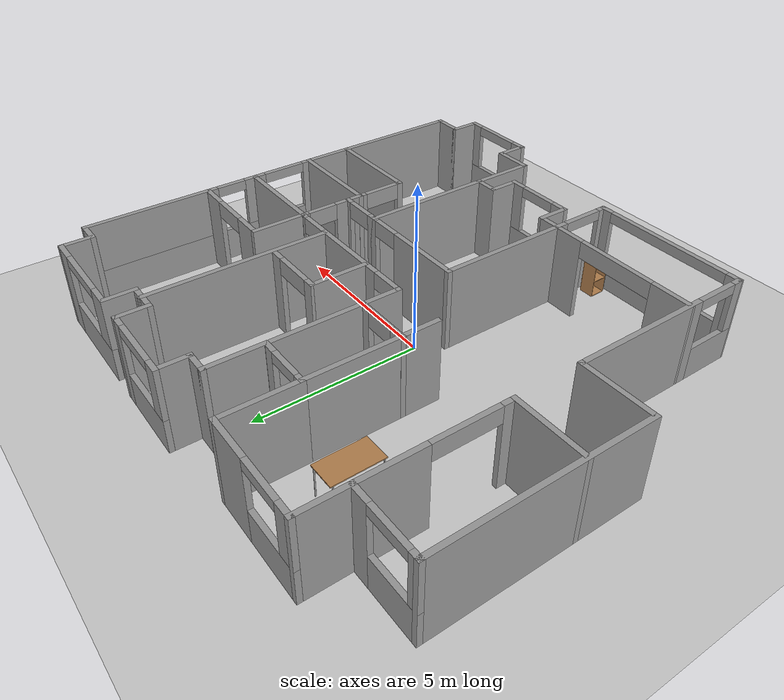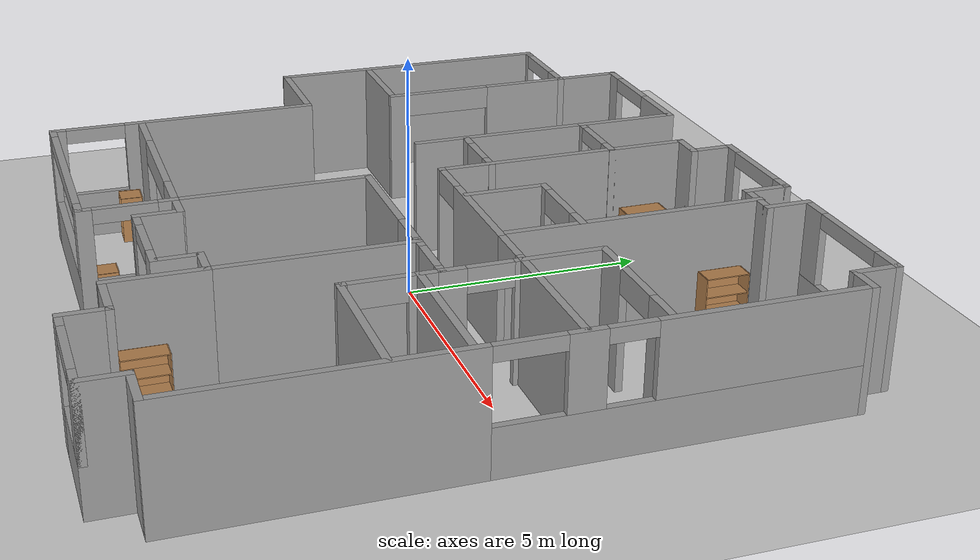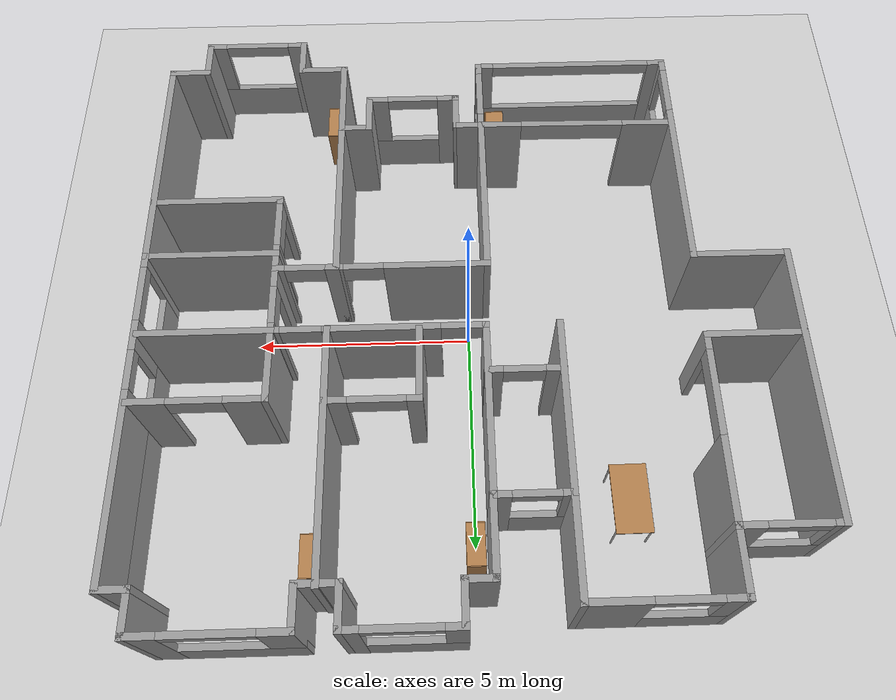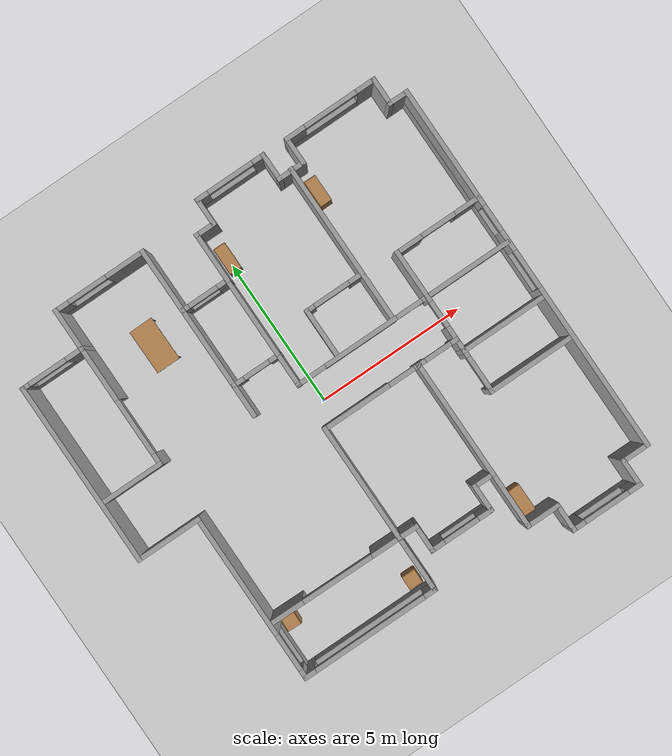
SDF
<sdf version="1.7">
 <world name="default">
  <light name="sun" type="directional">
   <pose>0 0 10 0 -0 0</pose>
   <diffuse>0.8 0.8 0.8 1</diffuse>
   <specular>0.2 0.2 0.2 1</specular>
   <attenuation>
    <range>1000</range>
    <constant>0.9</constant>
    <linear>0.01</linear>
    <quadratic>0.001</quadratic>
   </attenuation>
   <direction>-0.5 0.1 -0.9</direction>
   <spot><inner_angle>0</inner_angle><outer_angle>0</outer_angle><falloff>0</falloff></spot>
  </light>
  <model name="ground_plane">
   <static>1</static>
   <link name="link">
    <collision name="collision">
     <geometry><plane><normal>0 0 1</normal><size>100 100</size></plane></geometry>
     <surface>
      <contact><collide_bitmask>65535</collide_bitmask></contact>
      <friction><ode><mu>100</mu><mu2>50</mu2></ode></friction>
     </surface>
    </collision>
    <visual name="visual">
     <cast_shadows>0</cast_shadows>
     <geometry><plane><normal>0 0 1</normal><size>100 100</size></plane></geometry>
     <material>
      <script><uri>file://media/materials/scripts/gazebo.material</uri><name>Gazebo/Grey</name></script>
     </material>
    </visual>
   </link>
  </model>
  <gravity>0 0 -9.8</gravity>
  <magnetic_field>6e-06 2.3e-05 -4.2e-05</magnetic_field>
  <atmosphere type="adiabatic"/>
  <physics type="ode">
   <max_step_size>0.001</max_step_size>
   <real_time_factor>1</real_time_factor>
   <real_time_update_rate>1000</real_time_update_rate>
  </physics>
  <scene><ambient>0.4 0.4 0.4 1</ambient><background>0.7 0.7 0.7 1</background><shadows>1</shadows></scene>
  <spherical_coordinates>
   <surface_model>EARTH_WGS84</surface_model>
   <latitude_deg>0</latitude_deg>
   <longitude_deg>0</longitude_deg>
   <elevation>0</elevation>
   <heading_deg>0</heading_deg>
  </spherical_coordinates>
  <model name="house_0818_yt160_1">
   <pose>0.015299 -0.157746 0 0 -0 0</pose>
   <link name="Wall_0">
    <pose>-2.74999 -6.3 0 0 -0 0</pose>
    <visual name="Wall_0_Visual_0">
     <pose>-2.15818 0 1.25 0 -0 0</pose>
     <geometry><box><size>0.433633 0.15 2.5</size></box></geometry>
     <material>
      <script><uri>file://media/materials/scripts/gazebo.material</uri><name>Gazebo/Grey</name></script>
      <ambient>1 1 1 1</ambient>
     </material>
     <meta><layer>0</layer></meta>
    </visual>
    <collision name="Wall_0_Collision_0">
     <geometry><box><size>0.433633 0.15 2.5</size></box></geometry>
     <pose>-2.15818 0 1.25 0 -0 0</pose>
    </collision>
    <visual name="Wall_0_Visual_1">
     <pose>0.216816 0 0.5 0 -0 0</pose>
     <geometry><box><size>4.31637 0.15 1</size></box></geometry>
     <material>
      <script><uri>file://media/materials/scripts/gazebo.material</uri><name>Gazebo/Grey</name></script>
      <ambient>1 1 1 1</ambient>
     </material>
     <meta><layer>0</layer></meta>
    </visual>
    <collision name="Wall_0_Collision_1">
     <geometry><box><size>4.31637 0.15 1</size></box></geometry>
     <pose>0.216816 0 0.5 0 -0 0</pose>
    </collision>
    <visual name="Wall_0_Visual_2">
     <pose>2.15777 0 1.75 0 -0 0</pose>
     <geometry><box><size>0.434453 0.15 1.5</size></box></geometry>
     <material>
      <script><uri>file://media/materials/scripts/gazebo.material</uri><name>Gazebo/Grey</name></script>
      <ambient>1 1 1 1</ambient>
     </material>
     <meta><layer>0</layer></meta>
    </visual>
    <collision name="Wall_0_Collision_2">
     <geometry><box><size>0.434453 0.15 1.5</size></box></geometry>
     <pose>2.15777 0 1.75 0 -0 0</pose>
    </collision>
    <visual name="Wall_0_Visual_3">
     <pose>-0.00041 0 2.35 0 -0 0</pose>
     <geometry><box><size>3.88191 0.15 0.3</size></box></geometry>
     <material>
      <script><uri>file://media/materials/scripts/gazebo.material</uri><name>Gazebo/Grey</name></script>
      <ambient>1 1 1 1</ambient>
     </material>
     <meta><layer>0</layer></meta>
    </visual>
    <collision name="Wall_0_Collision_3">
     <geometry><box><size>3.88191 0.15 0.3</size></box></geometry>
     <pose>-0.00041 0 2.35 0 -0 0</pose>
    </collision>
   </link>
   <link name="Wall_1">
    <pose>-0.45 -5.3749 0 0 -0 1.57081</pose>
    <visual name="Wall_1_Visual_0">
     <pose>-0.838302 0 1.25 0 -0 0</pose>
     <geometry><box><size>0.323396 0.15 2.5</size></box></geometry>
     <material>
      <script><uri>file://media/materials/scripts/gazebo.material</uri><name>Gazebo/Grey</name></script>
      <ambient>1 1 1 1</ambient>
     </material>
     <meta><layer>0</layer></meta>
    </visual>
    <collision name="Wall_1_Collision_0">
     <geometry><box><size>0.323396 0.15 2.5</size></box></geometry>
     <pose>-0.838302 0 1.25 0 -0 0</pose>
    </collision>
    <visual name="Wall_1_Visual_1">
     <pose>0.161698 0 0.5 0 -0 0</pose>
     <geometry><box><size>1.6766 0.15 1</size></box></geometry>
     <material>
      <script><uri>file://media/materials/scripts/gazebo.material</uri><name>Gazebo/Grey</name></script>
      <ambient>1 1 1 1</ambient>
     </material>
     <meta><layer>0</layer></meta>
    </visual>
    <collision name="Wall_1_Collision_1">
     <geometry><box><size>1.6766 0.15 1</size></box></geometry>
     <pose>0.161698 0 0.5 0 -0 0</pose>
    </collision>
    <visual name="Wall_1_Visual_2">
     <pose>0.796698 0 1.75 0 -0 0</pose>
     <geometry><box><size>0.406604 0.15 1.5</size></box></geometry>
     <material>
      <script><uri>file://media/materials/scripts/gazebo.material</uri><name>Gazebo/Grey</name></script>
      <ambient>1 1 1 1</ambient>
     </material>
     <meta><layer>0</layer></meta>
    </visual>
    <collision name="Wall_1_Collision_2">
     <geometry><box><size>0.406604 0.15 1.5</size></box></geometry>
     <pose>0.796698 0 1.75 0 -0 0</pose>
    </collision>
    <visual name="Wall_1_Visual_3">
     <pose>-0.041604 0 2.35 0 -0 0</pose>
     <geometry><box><size>1.27 0.15 0.3</size></box></geometry>
     <material>
      <script><uri>file://media/materials/scripts/gazebo.material</uri><name>Gazebo/Grey</name></script>
      <ambient>1 1 1 1</ambient>
     </material>
     <meta><layer>0</layer></meta>
    </visual>
    <collision name="Wall_1_Collision_3">
     <geometry><box><size>1.27 0.15 0.3</size></box></geometry>
     <pose>-0.041604 0 2.35 0 -0 0</pose>
    </collision>
   </link>
   <link name="Wall_10">
    <collision name="Wall_10_Collision">
     <geometry><box><size>1.20003 0.15 2.5</size></box></geometry>
     <pose>0 0 1.25 0 -0 0</pose>
    </collision>
    <visual name="Wall_10_Visual">
     <pose>0 0 1.25 0 -0 0</pose>
     <geometry><box><size>1.20003 0.15 2.5</size></box></geometry>
     <material>
      <script><uri>file://media/materials/scripts/gazebo.material</uri><name>Gazebo/Grey</name></script>
      <ambient>1 1 1 1</ambient>
     </material>
     <meta><layer>0</layer></meta>
    </visual>
    <pose>3.42499 -6.29979 0 0 -0 0</pose>
   </link>
   <link name="Wall_11">
    <collision name="Wall_11_Collision">
     <geometry><box><size>1 0.15 2.5</size></box></geometry>
     <pose>0 0 1.25 0 -0 0</pose>
    </collision>
    <visual name="Wall_11_Visual">
     <pose>0 0 1.25 0 -0 0</pose>
     <geometry><box><size>1 0.15 2.5</size></box></geometry>
     <material>
      <script><uri>file://media/materials/scripts/gazebo.material</uri><name>Gazebo/Grey</name></script>
      <ambient>1 1 1 1</ambient>
     </material>
     <meta><layer>0</layer></meta>
    </visual>
    <pose>3.95 -6.7249 0 0 -0 -1.57076</pose>
   </link>
   <link name="Wall_12">
    <pose>5.12501 -7.15 0 0 -0 0</pose>
    <visual name="Wall_12_Visual_0">
     <pose>-1.00927 0 1.25 0 -0 0</pose>
     <geometry><box><size>0.481456 0.15 2.5</size></box></geometry>
     <material>
      <script><uri>file://media/materials/scripts/gazebo.material</uri><name>Gazebo/Grey</name></script>
      <ambient>1 1 1 1</ambient>
     </material>
     <meta><layer>0</layer></meta>
    </visual>
    <collision name="Wall_12_Collision_0">
     <geometry><box><size>0.481456 0.15 2.5</size></box></geometry>
     <pose>-1.00927 0 1.25 0 -0 0</pose>
    </collision>
    <visual name="Wall_12_Visual_1">
     <pose>0.240728 0 0.5 0 -0 0</pose>
     <geometry><box><size>2.01854 0.15 1</size></box></geometry>
     <material>
      <script><uri>file://media/materials/scripts/gazebo.material</uri><name>Gazebo/Grey</name></script>
      <ambient>1 1 1 1</ambient>
     </material>
     <meta><layer>0</layer></meta>
    </visual>
    <collision name="Wall_12_Collision_1">
     <geometry><box><size>2.01854 0.15 1</size></box></geometry>
     <pose>0.240728 0 0.5 0 -0 0</pose>
    </collision>
    <visual name="Wall_12_Visual_2">
     <pose>1.01273 0 1.75 0 -0 0</pose>
     <geometry><box><size>0.474544 0.15 1.5</size></box></geometry>
     <material>
      <script><uri>file://media/materials/scripts/gazebo.material</uri><name>Gazebo/Grey</name></script>
      <ambient>1 1 1 1</ambient>
     </material>
     <meta><layer>0</layer></meta>
    </visual>
    <collision name="Wall_12_Collision_2">
     <geometry><box><size>0.474544 0.15 1.5</size></box></geometry>
     <pose>1.01273 0 1.75 0 -0 0</pose>
    </collision>
    <visual name="Wall_12_Visual_3">
     <pose>0.003456 0 2.35 0 -0 0</pose>
     <geometry><box><size>1.544 0.15 0.3</size></box></geometry>
     <material>
      <script><uri>file://media/materials/scripts/gazebo.material</uri><name>Gazebo/Grey</name></script>
      <ambient>1 1 1 1</ambient>
     </material>
     <meta><layer>0</layer></meta>
    </visual>
    <collision name="Wall_12_Collision_3">
     <geometry><box><size>1.544 0.15 0.3</size></box></geometry>
     <pose>0.003456 0 2.35 0 -0 0</pose>
    </collision>
   </link>
   <link name="Wall_13">
    <collision name="Wall_13_Collision">
     <geometry><box><size>1 0.15 2.5</size></box></geometry>
     <pose>0 0 1.25 0 -0 0</pose>
    </collision>
    <visual name="Wall_13_Visual">
     <pose>0 0 1.25 0 -0 0</pose>
     <geometry><box><size>1 0.15 2.5</size></box></geometry>
     <material>
      <script><uri>file://media/materials/scripts/gazebo.material</uri><name>Gazebo/Grey</name></script>
      <ambient>1 1 1 1</ambient>
     </material>
     <meta><layer>0</layer></meta>
    </visual>
    <pose>6.30001 -6.725 0 0 -0 1.5708</pose>
   </link>
   <link name="Wall_16">
    <collision name="Wall_16_Collision">
     <geometry><box><size>1 0.15 2.5</size></box></geometry>
     <pose>0 0 1.25 0 -0 0</pose>
    </collision>
    <visual name="Wall_16_Visual">
     <pose>0 0 1.25 0 -0 0</pose>
     <geometry><box><size>1 0.15 2.5</size></box></geometry>
     <material>
      <script><uri>file://media/materials/scripts/gazebo.material</uri><name>Gazebo/Grey</name></script>
      <ambient>1 1 1 1</ambient>
     </material>
     <meta><layer>0</layer></meta>
    </visual>
    <pose>6.72501 -6.3 0 0 -0 0</pose>
   </link>
   <link name="Wall_17">
    <pose>7.15001 -0 0 0 -0 1.5708</pose>
    <visual name="Wall_17_Visual_0">
     <pose>-3.53052 0 1.25 0 -0 0</pose>
     <geometry><box><size>5.68897 0.15 2.5</size></box></geometry>
     <material>
      <script><uri>file://media/materials/scripts/gazebo.material</uri><name>Gazebo/Grey</name></script>
      <ambient>1 1 1 1</ambient>
     </material>
     <meta><layer>0</layer></meta>
    </visual>
    <collision name="Wall_17_Collision_0">
     <geometry><box><size>5.68897 0.15 2.5</size></box></geometry>
     <pose>-3.53052 0 1.25 0 -0 0</pose>
    </collision>
    <visual name="Wall_17_Visual_1">
     <pose>2.84448 0 0.5 0 -0 0</pose>
     <geometry><box><size>7.06103 0.15 1</size></box></geometry>
     <material>
      <script><uri>file://media/materials/scripts/gazebo.material</uri><name>Gazebo/Grey</name></script>
      <ambient>1 1 1 1</ambient>
     </material>
     <meta><layer>0</layer></meta>
    </visual>
    <collision name="Wall_17_Collision_1">
     <geometry><box><size>7.06103 0.15 1</size></box></geometry>
     <pose>2.84448 0 0.5 0 -0 0</pose>
    </collision>
    <visual name="Wall_17_Visual_2">
     <pose>0.990952 0 1.75 0 -0 0</pose>
     <geometry><box><size>0.703966 0.15 1.5</size></box></geometry>
     <material>
      <script><uri>file://media/materials/scripts/gazebo.material</uri><name>Gazebo/Grey</name></script>
      <ambient>1 1 1 1</ambient>
     </material>
     <meta><layer>0</layer></meta>
    </visual>
    <collision name="Wall_17_Collision_2">
     <geometry><box><size>0.703966 0.15 1.5</size></box></geometry>
     <pose>0.990952 0 1.75 0 -0 0</pose>
    </collision>
    <visual name="Wall_17_Visual_3">
     <pose>4.31147 0 1.75 0 -0 0</pose>
     <geometry><box><size>4.12706 0.15 1.5</size></box></geometry>
     <material>
      <script><uri>file://media/materials/scripts/gazebo.material</uri><name>Gazebo/Grey</name></script>
      <ambient>1 1 1 1</ambient>
     </material>
     <meta><layer>0</layer></meta>
    </visual>
    <collision name="Wall_17_Collision_3">
     <geometry><box><size>4.12706 0.15 1.5</size></box></geometry>
     <pose>4.31147 0 1.75 0 -0 0</pose>
    </collision>
    <visual name="Wall_17_Visual_4">
     <pose>-0.023532 0 2.35 0 -0 0</pose>
     <geometry><box><size>1.325 0.15 0.3</size></box></geometry>
     <material>
      <script><uri>file://media/materials/scripts/gazebo.material</uri><name>Gazebo/Grey</name></script>
      <ambient>1 1 1 1</ambient>
     </material>
     <meta><layer>0</layer></meta>
    </visual>
    <collision name="Wall_17_Collision_4">
     <geometry><box><size>1.325 0.15 0.3</size></box></geometry>
     <pose>-0.023532 0 2.35 0 -0 0</pose>
    </collision>
    <visual name="Wall_17_Visual_5">
     <pose>1.79543 0 2.35 0 -0 0</pose>
     <geometry><box><size>0.905 0.15 0.3</size></box></geometry>
     <material>
      <script><uri>file://media/materials/scripts/gazebo.material</uri><name>Gazebo/Grey</name></script>
      <ambient>1 1 1 1</ambient>
     </material>
     <meta><layer>0</layer></meta>
    </visual>
    <collision name="Wall_17_Collision_5">
     <geometry><box><size>0.905 0.15 0.3</size></box></geometry>
     <pose>1.79543 0 2.35 0 -0 0</pose>
    </collision>
   </link>
   <link name="Wall_18">
    <collision name="Wall_18_Collision">
     <geometry><box><size>0.75 0.15 2.5</size></box></geometry>
     <pose>0 0 1.25 0 -0 0</pose>
    </collision>
    <visual name="Wall_18_Visual">
     <pose>0 0 1.25 0 -0 0</pose>
     <geometry><box><size>0.75 0.15 2.5</size></box></geometry>
     <material>
      <script><uri>file://media/materials/scripts/gazebo.material</uri><name>Gazebo/Grey</name></script>
      <ambient>1 1 1 1</ambient>
     </material>
     <meta><layer>0</layer></meta>
    </visual>
    <pose>6.85001 6.3 0 0 -0 3.14159</pose>
   </link>
   <link name="Wall_2">
    <collision name="Wall_2_Collision">
     <geometry><box><size>0.75 0.15 2.5</size></box></geometry>
     <pose>0 0 1.25 0 -0 0</pose>
    </collision>
    <visual name="Wall_2_Visual">
     <pose>0 0 1.25 0 -0 0</pose>
     <geometry><box><size>0.75 0.15 2.5</size></box></geometry>
     <material>
      <script><uri>file://media/materials/scripts/gazebo.material</uri><name>Gazebo/Grey</name></script>
      <ambient>1 1 1 1</ambient>
     </material>
     <meta><layer>0</layer></meta>
    </visual>
    <pose>-0.15 -4.4499 0 0 -0 -0.000342</pose>
   </link>
   <link name="Wall_20">
    <collision name="Wall_20_Collision">
     <geometry><box><size>1 0.15 2.5</size></box></geometry>
     <pose>0 0 1.25 0 -0 0</pose>
    </collision>
    <visual name="Wall_20_Visual">
     <pose>0 0 1.25 0 -0 0</pose>
     <geometry><box><size>1 0.15 2.5</size></box></geometry>
     <material>
      <script><uri>file://media/materials/scripts/gazebo.material</uri><name>Gazebo/Grey</name></script>
      <ambient>1 1 1 1</ambient>
     </material>
     <meta><layer>0</layer></meta>
    </visual>
    <pose>6.55001 6.725 0 0 -0 1.5708</pose>
   </link>
   <link name="Wall_21">
    <pose>5.00001 7.15 0 0 -0 3.14159</pose>
    <visual name="Wall_21_Visual_0">
     <pose>-1.26954 0 1.25 0 -0 0</pose>
     <geometry><box><size>0.710929 0.15 2.5</size></box></geometry>
     <material>
      <script><uri>file://media/materials/scripts/gazebo.material</uri><name>Gazebo/Grey</name></script>
      <ambient>1 1 1 1</ambient>
     </material>
     <meta><layer>0</layer></meta>
    </visual>
    <collision name="Wall_21_Collision_0">
     <geometry><box><size>0.710929 0.15 2.5</size></box></geometry>
     <pose>-1.26954 0 1.25 0 -0 0</pose>
    </collision>
    <visual name="Wall_21_Visual_1">
     <pose>0.355464 0 0.5 0 -0 0</pose>
     <geometry><box><size>2.53907 0.15 1</size></box></geometry>
     <material>
      <script><uri>file://media/materials/scripts/gazebo.material</uri><name>Gazebo/Grey</name></script>
      <ambient>1 1 1 1</ambient>
     </material>
     <meta><layer>0</layer></meta>
    </visual>
    <collision name="Wall_21_Collision_1">
     <geometry><box><size>2.53907 0.15 1</size></box></geometry>
     <pose>0.355464 0 0.5 0 -0 0</pose>
    </collision>
    <visual name="Wall_21_Visual_2">
     <pose>1.27146 0 1.75 0 -0 0</pose>
     <geometry><box><size>0.707071 0.15 1.5</size></box></geometry>
     <material>
      <script><uri>file://media/materials/scripts/gazebo.material</uri><name>Gazebo/Grey</name></script>
      <ambient>1 1 1 1</ambient>
     </material>
     <meta><layer>0</layer></meta>
    </visual>
    <collision name="Wall_21_Collision_2">
     <geometry><box><size>0.707071 0.15 1.5</size></box></geometry>
     <pose>1.27146 0 1.75 0 -0 0</pose>
    </collision>
    <visual name="Wall_21_Visual_3">
     <pose>0.001929 0 2.35 0 -0 0</pose>
     <geometry><box><size>1.832 0.15 0.3</size></box></geometry>
     <material>
      <script><uri>file://media/materials/scripts/gazebo.material</uri><name>Gazebo/Grey</name></script>
      <ambient>1 1 1 1</ambient>
     </material>
     <meta><layer>0</layer></meta>
    </visual>
    <collision name="Wall_21_Collision_3">
     <geometry><box><size>1.832 0.15 0.3</size></box></geometry>
     <pose>0.001929 0 2.35 0 -0 0</pose>
    </collision>
   </link>
   <link name="Wall_22">
    <collision name="Wall_22_Collision">
     <geometry><box><size>1 0.15 2.5</size></box></geometry>
     <pose>0 0 1.25 0 -0 0</pose>
    </collision>
    <visual name="Wall_22_Visual">
     <pose>0 0 1.25 0 -0 0</pose>
     <geometry><box><size>1 0.15 2.5</size></box></geometry>
     <material>
      <script><uri>file://media/materials/scripts/gazebo.material</uri><name>Gazebo/Grey</name></script>
      <ambient>1 1 1 1</ambient>
     </material>
     <meta><layer>0</layer></meta>
    </visual>
    <pose>3.45001 6.725 0 0 -0 -1.5708</pose>
   </link>
   <link name="Wall_23">
    <collision name="Wall_23_Collision">
     <geometry><box><size>1 0.15 2.5</size></box></geometry>
     <pose>0 0 1.25 0 -0 0</pose>
    </collision>
    <visual name="Wall_23_Visual">
     <pose>0 0 1.25 0 -0 0</pose>
     <geometry><box><size>1 0.15 2.5</size></box></geometry>
     <material>
      <script><uri>file://media/materials/scripts/gazebo.material</uri><name>Gazebo/Grey</name></script>
      <ambient>1 1 1 1</ambient>
     </material>
     <meta><layer>0</layer></meta>
    </visual>
    <pose>3.02501 6.3 0 0 -0 3.14159</pose>
   </link>
   <link name="Wall_24">
    <collision name="Wall_24_Collision">
     <geometry><box><size>1 0.15 2.5</size></box></geometry>
     <pose>0 0 1.25 0 -0 0</pose>
    </collision>
    <visual name="Wall_24_Visual">
     <pose>0 0 1.25 0 -0 0</pose>
     <geometry><box><size>1 0.15 2.5</size></box></geometry>
     <material>
      <script><uri>file://media/materials/scripts/gazebo.material</uri><name>Gazebo/Grey</name></script>
      <ambient>1 1 1 1</ambient>
     </material>
     <meta><layer>0</layer></meta>
    </visual>
    <pose>2.60001 6.725 0 0 -0 1.5708</pose>
   </link>
   <link name="Wall_25">
    <pose>1.42501 7.15 0 0 -0 3.14159</pose>
    <visual name="Wall_25_Visual_0">
     <pose>-1.01884 0 1.25 0 -0 0</pose>
     <geometry><box><size>0.462315 0.15 2.5</size></box></geometry>
     <material>
      <script><uri>file://media/materials/scripts/gazebo.material</uri><name>Gazebo/Grey</name></script>
      <ambient>1 1 1 1</ambient>
     </material>
     <meta><layer>0</layer></meta>
    </visual>
    <collision name="Wall_25_Collision_0">
     <geometry><box><size>0.462315 0.15 2.5</size></box></geometry>
     <pose>-1.01884 0 1.25 0 -0 0</pose>
    </collision>
    <visual name="Wall_25_Visual_1">
     <pose>0.231157 0 0.5 0 -0 0</pose>
     <geometry><box><size>2.03769 0.15 1</size></box></geometry>
     <material>
      <script><uri>file://media/materials/scripts/gazebo.material</uri><name>Gazebo/Grey</name></script>
      <ambient>1 1 1 1</ambient>
     </material>
     <meta><layer>0</layer></meta>
    </visual>
    <collision name="Wall_25_Collision_1">
     <geometry><box><size>2.03769 0.15 1</size></box></geometry>
     <pose>0.231157 0 0.5 0 -0 0</pose>
    </collision>
    <visual name="Wall_25_Visual_2">
     <pose>1.0213 0 1.75 0 -0 0</pose>
     <geometry><box><size>0.45741 0.15 1.5</size></box></geometry>
     <material>
      <script><uri>file://media/materials/scripts/gazebo.material</uri><name>Gazebo/Grey</name></script>
      <ambient>1 1 1 1</ambient>
     </material>
     <meta><layer>0</layer></meta>
    </visual>
    <collision name="Wall_25_Collision_2">
     <geometry><box><size>0.45741 0.15 1.5</size></box></geometry>
     <pose>1.0213 0 1.75 0 -0 0</pose>
    </collision>
    <visual name="Wall_25_Visual_3">
     <pose>0.002452 0 2.35 0 -0 0</pose>
     <geometry><box><size>1.58028 0.15 0.3</size></box></geometry>
     <material>
      <script><uri>file://media/materials/scripts/gazebo.material</uri><name>Gazebo/Grey</name></script>
      <ambient>1 1 1 1</ambient>
     </material>
     <meta><layer>0</layer></meta>
    </visual>
    <collision name="Wall_25_Collision_3">
     <geometry><box><size>1.58028 0.15 0.3</size></box></geometry>
     <pose>0.002452 0 2.35 0 -0 0</pose>
    </collision>
   </link>
   <link name="Wall_26">
    <collision name="Wall_26_Collision">
     <geometry><box><size>1 0.15 2.5</size></box></geometry>
     <pose>0 0 1.25 0 -0 0</pose>
    </collision>
    <visual name="Wall_26_Visual">
     <pose>0 0 1.25 0 -0 0</pose>
     <geometry><box><size>1 0.15 2.5</size></box></geometry>
     <material>
      <script><uri>file://media/materials/scripts/gazebo.material</uri><name>Gazebo/Grey</name></script>
      <ambient>1 1 1 1</ambient>
     </material>
     <meta><layer>0</layer></meta>
    </visual>
    <pose>0.250013 6.725 0 0 -0 -1.5708</pose>
   </link>
   <link name="Wall_27">
    <collision name="Wall_27_Collision">
     <geometry><box><size>0.75 0.15 2.5</size></box></geometry>
     <pose>0 0 1.25 0 -0 0</pose>
    </collision>
    <visual name="Wall_27_Visual">
     <pose>0 0 1.25 0 -0 0</pose>
     <geometry><box><size>0.75 0.15 2.5</size></box></geometry>
     <material>
      <script><uri>file://media/materials/scripts/gazebo.material</uri><name>Gazebo/Grey</name></script>
      <ambient>1 1 1 1</ambient>
     </material>
     <meta><layer>0</layer></meta>
    </visual>
    <pose>-0.049987 6.3 0 0 -0 3.14159</pose>
   </link>
   <link name="Wall_28">
    <collision name="Wall_28_Collision">
     <geometry><box><size>1.75 0.15 2.5</size></box></geometry>
     <pose>0 0 1.25 0 -0 0</pose>
    </collision>
    <visual name="Wall_28_Visual">
     <pose>0 0 1.25 0 -0 0</pose>
     <geometry><box><size>1.75 0.15 2.5</size></box></geometry>
     <material>
      <script><uri>file://media/materials/scripts/gazebo.material</uri><name>Gazebo/Grey</name></script>
      <ambient>1 1 1 1</ambient>
     </material>
     <meta><layer>0</layer></meta>
    </visual>
    <pose>-0.349987 5.5 0 0 -0 -1.5708</pose>
   </link>
   <link name="Wall_29">
    <pose>-1.15 4.7001 0 0 -0 3.14146</pose>
    <visual name="Wall_29_Visual_0">
     <pose>-0.650791 0 1.25 0 -0 0</pose>
     <geometry><box><size>0.448418 0.15 2.5</size></box></geometry>
     <material>
      <script><uri>file://media/materials/scripts/gazebo.material</uri><name>Gazebo/Grey</name></script>
      <ambient>1 1 1 1</ambient>
     </material>
     <meta><layer>0</layer></meta>
    </visual>
    <collision name="Wall_29_Collision_0">
     <geometry><box><size>0.448418 0.15 2.5</size></box></geometry>
     <pose>-0.650791 0 1.25 0 -0 0</pose>
    </collision>
    <visual name="Wall_29_Visual_1">
     <pose>0.224209 0 0.5 0 -0 0</pose>
     <geometry><box><size>1.30158 0.15 1</size></box></geometry>
     <material>
      <script><uri>file://media/materials/scripts/gazebo.material</uri><name>Gazebo/Grey</name></script>
      <ambient>1 1 1 1</ambient>
     </material>
     <meta><layer>0</layer></meta>
    </visual>
    <collision name="Wall_29_Collision_1">
     <geometry><box><size>1.30158 0.15 1</size></box></geometry>
     <pose>0.224209 0 0.5 0 -0 0</pose>
    </collision>
    <visual name="Wall_29_Visual_2">
     <pose>0.723209 0 1.75 0 -0 0</pose>
     <geometry><box><size>0.303582 0.15 1.5</size></box></geometry>
     <material>
      <script><uri>file://media/materials/scripts/gazebo.material</uri><name>Gazebo/Grey</name></script>
      <ambient>1 1 1 1</ambient>
     </material>
     <meta><layer>0</layer></meta>
    </visual>
    <collision name="Wall_29_Collision_2">
     <geometry><box><size>0.303582 0.15 1.5</size></box></geometry>
     <pose>0.723209 0 1.75 0 -0 0</pose>
    </collision>
    <visual name="Wall_29_Visual_3">
     <pose>0.072418 0 2.35 0 -0 0</pose>
     <geometry><box><size>0.998 0.15 0.3</size></box></geometry>
     <material>
      <script><uri>file://media/materials/scripts/gazebo.material</uri><name>Gazebo/Grey</name></script>
      <ambient>1 1 1 1</ambient>
     </material>
     <meta><layer>0</layer></meta>
    </visual>
    <collision name="Wall_29_Collision_3">
     <geometry><box><size>0.998 0.15 0.3</size></box></geometry>
     <pose>0.072418 0 2.35 0 -0 0</pose>
    </collision>
   </link>
   <link name="Wall_3">
    <collision name="Wall_3_Collision">
     <geometry><box><size>1 0.15 2.5</size></box></geometry>
     <pose>0 0 1.25 0 -0 0</pose>
    </collision>
    <visual name="Wall_3_Visual">
     <pose>0 0 1.25 0 -0 0</pose>
     <geometry><box><size>1 0.15 2.5</size></box></geometry>
     <material>
      <script><uri>file://media/materials/scripts/gazebo.material</uri><name>Gazebo/Grey</name></script>
      <ambient>1 1 1 1</ambient>
     </material>
     <meta><layer>0</layer></meta>
    </visual>
    <pose>0.150013 -4.875 0 0 -0 -1.5708</pose>
   </link>
   <link name="Wall_30">
    <collision name="Wall_30_Collision">
     <geometry><box><size>2.25 0.15 2.5</size></box></geometry>
     <pose>0 0 1.25 0 -0 0</pose>
    </collision>
    <visual name="Wall_30_Visual">
     <pose>0 0 1.25 0 -0 0</pose>
     <geometry><box><size>2.25 0.15 2.5</size></box></geometry>
     <material>
      <script><uri>file://media/materials/scripts/gazebo.material</uri><name>Gazebo/Grey</name></script>
      <ambient>1 1 1 1</ambient>
     </material>
     <meta><layer>0</layer></meta>
    </visual>
    <pose>-1.95 5.7501 0 0 -0 1.57078</pose>
   </link>
   <link name="Wall_31">
    <pose>-3.49999 6.8 0 0 -0 3.14159</pose>
    <visual name="Wall_31_Visual_0">
     <pose>-0.931268 0 1.25 0 -0 0</pose>
     <geometry><box><size>1.38746 0.15 2.5</size></box></geometry>
     <material>
      <script><uri>file://media/materials/scripts/gazebo.material</uri><name>Gazebo/Grey</name></script>
      <ambient>1 1 1 1</ambient>
     </material>
     <meta><layer>0</layer></meta>
    </visual>
    <collision name="Wall_31_Collision_0">
     <geometry><box><size>1.38746 0.15 2.5</size></box></geometry>
     <pose>-0.931268 0 1.25 0 -0 0</pose>
    </collision>
    <visual name="Wall_31_Visual_1">
     <pose>0.693732 0 0.5 0 -0 0</pose>
     <geometry><box><size>1.86254 0.15 1</size></box></geometry>
     <material>
      <script><uri>file://media/materials/scripts/gazebo.material</uri><name>Gazebo/Grey</name></script>
      <ambient>1 1 1 1</ambient>
     </material>
     <meta><layer>0</layer></meta>
    </visual>
    <collision name="Wall_31_Collision_1">
     <geometry><box><size>1.86254 0.15 1</size></box></geometry>
     <pose>0.693732 0 0.5 0 -0 0</pose>
    </collision>
    <visual name="Wall_31_Visual_2">
     <pose>1.35823 0 1.75 0 -0 0</pose>
     <geometry><box><size>0.533535 0.15 1.5</size></box></geometry>
     <material>
      <script><uri>file://media/materials/scripts/gazebo.material</uri><name>Gazebo/Grey</name></script>
      <ambient>1 1 1 1</ambient>
     </material>
     <meta><layer>0</layer></meta>
    </visual>
    <collision name="Wall_31_Collision_2">
     <geometry><box><size>0.533535 0.15 1.5</size></box></geometry>
     <pose>1.35823 0 1.75 0 -0 0</pose>
    </collision>
    <visual name="Wall_31_Visual_3">
     <pose>0.426965 0 2.35 0 -0 0</pose>
     <geometry><box><size>1.329 0.15 0.3</size></box></geometry>
     <material>
      <script><uri>file://media/materials/scripts/gazebo.material</uri><name>Gazebo/Grey</name></script>
      <ambient>1 1 1 1</ambient>
     </material>
     <meta><layer>0</layer></meta>
    </visual>
    <collision name="Wall_31_Collision_3">
     <geometry><box><size>1.329 0.15 0.3</size></box></geometry>
     <pose>0.426965 0 2.35 0 -0 0</pose>
    </collision>
   </link>
   <link name="Wall_32">
    <collision name="Wall_32_Collision">
     <geometry><box><size>1.5 0.15 2.5</size></box></geometry>
     <pose>0 0 1.25 0 -0 0</pose>
    </collision>
    <visual name="Wall_32_Visual">
     <pose>0 0 1.25 0 -0 0</pose>
     <geometry><box><size>1.5 0.15 2.5</size></box></geometry>
     <material>
      <script><uri>file://media/materials/scripts/gazebo.material</uri><name>Gazebo/Grey</name></script>
      <ambient>1 1 1 1</ambient>
     </material>
     <meta><layer>0</layer></meta>
    </visual>
    <pose>-5.05 6.1251 0 0 -0 -1.57082</pose>
   </link>
   <link name="Wall_33">
    <pose>-6.1 5.4501 0 0 -0 -3.14149</pose>
    <visual name="Wall_33_Visual_0">
     <pose>-0.80389 0 1.25 0 -0 0</pose>
     <geometry><box><size>0.642221 0.15 2.5</size></box></geometry>
     <material>
      <script><uri>file://media/materials/scripts/gazebo.material</uri><name>Gazebo/Grey</name></script>
      <ambient>1 1 1 1</ambient>
     </material>
     <meta><layer>0</layer></meta>
    </visual>
    <collision name="Wall_33_Collision_0">
     <geometry><box><size>0.642221 0.15 2.5</size></box></geometry>
     <pose>-0.80389 0 1.25 0 -0 0</pose>
    </collision>
    <visual name="Wall_33_Visual_1">
     <pose>0.32111 0 0.5 0 -0 0</pose>
     <geometry><box><size>1.60778 0.15 1</size></box></geometry>
     <material>
      <script><uri>file://media/materials/scripts/gazebo.material</uri><name>Gazebo/Grey</name></script>
      <ambient>1 1 1 1</ambient>
     </material>
     <meta><layer>0</layer></meta>
    </visual>
    <collision name="Wall_33_Collision_1">
     <geometry><box><size>1.60778 0.15 1</size></box></geometry>
     <pose>0.32111 0 0.5 0 -0 0</pose>
    </collision>
    <visual name="Wall_33_Visual_2">
     <pose>0.97211 0 1.75 0 -0 0</pose>
     <geometry><box><size>0.305779 0.15 1.5</size></box></geometry>
     <material>
      <script><uri>file://media/materials/scripts/gazebo.material</uri><name>Gazebo/Grey</name></script>
      <ambient>1 1 1 1</ambient>
     </material>
     <meta><layer>0</layer></meta>
    </visual>
    <collision name="Wall_33_Collision_2">
     <geometry><box><size>0.305779 0.15 1.5</size></box></geometry>
     <pose>0.97211 0 1.75 0 -0 0</pose>
    </collision>
    <visual name="Wall_33_Visual_3">
     <pose>0.168221 0 2.35 0 -0 0</pose>
     <geometry><box><size>1.302 0.15 0.3</size></box></geometry>
     <material>
      <script><uri>file://media/materials/scripts/gazebo.material</uri><name>Gazebo/Grey</name></script>
      <ambient>1 1 1 1</ambient>
     </material>
     <meta><layer>0</layer></meta>
    </visual>
    <collision name="Wall_33_Collision_3">
     <geometry><box><size>1.302 0.15 0.3</size></box></geometry>
     <pose>0.168221 0 2.35 0 -0 0</pose>
    </collision>
   </link>
   <link name="Wall_34">
    <collision name="Wall_34_Collision">
     <geometry><box><size>6.25 0.15 2.5</size></box></geometry>
     <pose>0 0 1.25 0 -0 0</pose>
    </collision>
    <visual name="Wall_34_Visual">
     <pose>0 0 1.25 0 -0 0</pose>
     <geometry><box><size>6.25 0.15 2.5</size></box></geometry>
     <material>
      <script><uri>file://media/materials/scripts/gazebo.material</uri><name>Gazebo/Grey</name></script>
      <ambient>1 1 1 1</ambient>
     </material>
     <meta><layer>0</layer></meta>
    </visual>
    <pose>-7.14999 2.4 0 0 -0 -1.5708</pose>
   </link>
   <link name="Wall_35">
    <collision name="Wall_35_Collision">
     <geometry><box><size>2.25 0.15 2.5</size></box></geometry>
     <pose>0 0 1.25 0 -0 0</pose>
    </collision>
    <visual name="Wall_35_Visual">
     <pose>0 0 1.25 0 -0 0</pose>
     <geometry><box><size>2.25 0.15 2.5</size></box></geometry>
     <material>
      <script><uri>file://media/materials/scripts/gazebo.material</uri><name>Gazebo/Grey</name></script>
      <ambient>1 1 1 1</ambient>
     </material>
     <meta><layer>0</layer></meta>
    </visual>
    <pose>-6.09999 -0.65 0 0 -0 0</pose>
   </link>
   <link name="Wall_36">
    <pose>-5.04999 -3.45 0 0 -0 -1.5708</pose>
    <visual name="Wall_36_Visual_0">
     <pose>-0.775854 0 1.25 0 -0 0</pose>
     <geometry><box><size>4.19829 0.15 2.5</size></box></geometry>
     <material>
      <script><uri>file://media/materials/scripts/gazebo.material</uri><name>Gazebo/Grey</name></script>
      <ambient>1 1 1 1</ambient>
     </material>
     <meta><layer>0</layer></meta>
    </visual>
    <collision name="Wall_36_Collision_0">
     <geometry><box><size>4.19829 0.15 2.5</size></box></geometry>
     <pose>-0.775854 0 1.25 0 -0 0</pose>
    </collision>
    <visual name="Wall_36_Visual_1">
     <pose>2.09915 0 0.5 0 -0 0</pose>
     <geometry><box><size>1.55171 0.15 1</size></box></geometry>
     <material>
      <script><uri>file://media/materials/scripts/gazebo.material</uri><name>Gazebo/Grey</name></script>
      <ambient>1 1 1 1</ambient>
     </material>
     <meta><layer>0</layer></meta>
    </visual>
    <collision name="Wall_36_Collision_1">
     <geometry><box><size>1.55171 0.15 1</size></box></geometry>
     <pose>2.09915 0 0.5 0 -0 0</pose>
    </collision>
    <visual name="Wall_36_Visual_2">
     <pose>2.72715 0 1.75 0 -0 0</pose>
     <geometry><box><size>0.295708 0.15 1.5</size></box></geometry>
     <material>
      <script><uri>file://media/materials/scripts/gazebo.material</uri><name>Gazebo/Grey</name></script>
      <ambient>1 1 1 1</ambient>
     </material>
     <meta><layer>0</layer></meta>
    </visual>
    <collision name="Wall_36_Collision_2">
     <geometry><box><size>0.295708 0.15 1.5</size></box></geometry>
     <pose>2.72715 0 1.75 0 -0 0</pose>
    </collision>
    <visual name="Wall_36_Visual_3">
     <pose>1.95129 0 2.35 0 -0 0</pose>
     <geometry><box><size>1.256 0.15 0.3</size></box></geometry>
     <material>
      <script><uri>file://media/materials/scripts/gazebo.material</uri><name>Gazebo/Grey</name></script>
      <ambient>1 1 1 1</ambient>
     </material>
     <meta><layer>0</layer></meta>
    </visual>
    <collision name="Wall_36_Collision_3">
     <geometry><box><size>1.256 0.15 0.3</size></box></geometry>
     <pose>1.95129 0 2.35 0 -0 0</pose>
    </collision>
   </link>
   <link name="Wall_38">
    <pose>-2.75001 -4.4253 0 0 -0 -0.010652</pose>
    <visual name="Wall_38_Visual_0">
     <pose>-1.74086 0 1.25 0 -0 0</pose>
     <geometry><box><size>1.26858 0.15 2.5</size></box></geometry>
     <material>
      <script><uri>file://media/materials/scripts/gazebo.material</uri><name>Gazebo/Grey</name></script>
      <ambient>1 1 1 1</ambient>
     </material>
     <meta><layer>0</layer></meta>
    </visual>
    <collision name="Wall_38_Collision_0">
     <geometry><box><size>1.26858 0.15 2.5</size></box></geometry>
     <pose>-1.74086 0 1.25 0 -0 0</pose>
    </collision>
    <visual name="Wall_38_Visual_1">
     <pose>1.85196 0 1.25 0 -0 0</pose>
     <geometry><box><size>1.04636 0.15 2.5</size></box></geometry>
     <material>
      <script><uri>file://media/materials/scripts/gazebo.material</uri><name>Gazebo/Grey</name></script>
      <ambient>1 1 1 1</ambient>
     </material>
     <meta><layer>0</layer></meta>
    </visual>
    <collision name="Wall_38_Collision_1">
     <geometry><box><size>1.04636 0.15 2.5</size></box></geometry>
     <pose>1.85196 0 1.25 0 -0 0</pose>
    </collision>
    <visual name="Wall_38_Visual_2">
     <pose>0.111105 0 2.25 0 -0 0</pose>
     <geometry><box><size>2.43535 0.15 0.5</size></box></geometry>
     <material>
      <script><uri>file://media/materials/scripts/gazebo.material</uri><name>Gazebo/Grey</name></script>
      <ambient>1 1 1 1</ambient>
     </material>
     <meta><layer>0</layer></meta>
    </visual>
    <collision name="Wall_38_Collision_2">
     <geometry><box><size>2.43535 0.15 0.5</size></box></geometry>
     <pose>0.111105 0 2.25 0 -0 0</pose>
    </collision>
   </link>
   <link name="Wall_40">
    <collision name="Wall_40_Collision">
     <geometry><box><size>4.04023 0.15 2.5</size></box></geometry>
     <pose>0 0 1.25 0 -0 0</pose>
    </collision>
    <visual name="Wall_40_Visual">
     <pose>0 0 1.25 0 -0 0</pose>
     <geometry><box><size>4.04023 0.15 2.5</size></box></geometry>
     <material>
      <script><uri>file://media/materials/scripts/gazebo.material</uri><name>Gazebo/Grey</name></script>
      <ambient>1 1 1 1</ambient>
     </material>
     <meta><layer>0</layer></meta>
    </visual>
    <pose>-0.450014 -2.5048 0 0 -0 1.5708</pose>
   </link>
   <link name="Wall_41">
    <pose>1.22499 -0.559795 0 0 -0 0</pose>
    <visual name="Wall_41_Visual_0">
     <pose>-0.561728 0 1.25 0 -0 0</pose>
     <geometry><box><size>2.3766 0.15 2.5</size></box></geometry>
     <material>
      <script><uri>file://media/materials/scripts/gazebo.material</uri><name>Gazebo/Grey</name></script>
      <ambient>1 1 1 1</ambient>
     </material>
     <meta><layer>0</layer></meta>
    </visual>
    <collision name="Wall_41_Collision_0">
     <geometry><box><size>2.3766 0.15 2.5</size></box></geometry>
     <pose>-0.561728 0 1.25 0 -0 0</pose>
    </collision>
    <visual name="Wall_41_Visual_1">
     <pose>1.6383 0 1.25 0 -0 0</pose>
     <geometry><box><size>0.223456 0.15 2.5</size></box></geometry>
     <material>
      <script><uri>file://media/materials/scripts/gazebo.material</uri><name>Gazebo/Grey</name></script>
      <ambient>1 1 1 1</ambient>
     </material>
     <meta><layer>0</layer></meta>
    </visual>
    <collision name="Wall_41_Collision_1">
     <geometry><box><size>0.223456 0.15 2.5</size></box></geometry>
     <pose>1.6383 0 1.25 0 -0 0</pose>
    </collision>
    <visual name="Wall_41_Visual_2">
     <pose>1.07657 0 2.25 0 -0 0</pose>
     <geometry><box><size>0.9 0.15 0.5</size></box></geometry>
     <material>
      <script><uri>file://media/materials/scripts/gazebo.material</uri><name>Gazebo/Grey</name></script>
      <ambient>1 1 1 1</ambient>
     </material>
     <meta><layer>0</layer></meta>
    </visual>
    <collision name="Wall_41_Collision_2">
     <geometry><box><size>0.9 0.15 0.5</size></box></geometry>
     <pose>1.07657 0 2.25 0 -0 0</pose>
    </collision>
   </link>
   <link name="Wall_42">
    <collision name="Wall_42_Collision">
     <geometry><box><size>4.04 0.15 2.5</size></box></geometry>
     <pose>0 0 1.25 0 -0 0</pose>
    </collision>
    <visual name="Wall_42_Visual">
     <pose>0 0 1.25 0 -0 0</pose>
     <geometry><box><size>4.04 0.15 2.5</size></box></geometry>
     <material>
      <script><uri>file://media/materials/scripts/gazebo.material</uri><name>Gazebo/Grey</name></script>
      <ambient>1 1 1 1</ambient>
     </material>
     <meta><layer>0</layer></meta>
    </visual>
    <pose>2.89999 -2.5048 0 0 -0 -1.5708</pose>
   </link>
   <link name="Wall_44">
    <pose>3.57499 -0.559795 0 0 -0 0</pose>
    <visual name="Wall_44_Visual_0">
     <pose>-0.589056 0 1.25 0 -0 0</pose>
     <geometry><box><size>0.321888 0.15 2.5</size></box></geometry>
     <material>
      <script><uri>file://media/materials/scripts/gazebo.material</uri><name>Gazebo/Grey</name></script>
      <ambient>1 1 1 1</ambient>
     </material>
     <meta><layer>0</layer></meta>
    </visual>
    <collision name="Wall_44_Collision_0">
     <geometry><box><size>0.321888 0.15 2.5</size></box></geometry>
     <pose>-0.589056 0 1.25 0 -0 0</pose>
    </collision>
    <visual name="Wall_44_Visual_1">
     <pose>0.610944 0 1.25 0 -0 0</pose>
     <geometry><box><size>0.278112 0.15 2.5</size></box></geometry>
     <material>
      <script><uri>file://media/materials/scripts/gazebo.material</uri><name>Gazebo/Grey</name></script>
      <ambient>1 1 1 1</ambient>
     </material>
     <meta><layer>0</layer></meta>
    </visual>
    <collision name="Wall_44_Collision_1">
     <geometry><box><size>0.278112 0.15 2.5</size></box></geometry>
     <pose>0.610944 0 1.25 0 -0 0</pose>
    </collision>
    <visual name="Wall_44_Visual_2">
     <pose>0.021888 0 2.25 0 -0 0</pose>
     <geometry><box><size>0.9 0.15 0.5</size></box></geometry>
     <material>
      <script><uri>file://media/materials/scripts/gazebo.material</uri><name>Gazebo/Grey</name></script>
      <ambient>1 1 1 1</ambient>
     </material>
     <meta><layer>0</layer></meta>
    </visual>
    <collision name="Wall_44_Collision_2">
     <geometry><box><size>0.9 0.15 0.5</size></box></geometry>
     <pose>0.021888 0 2.25 0 -0 0</pose>
    </collision>
   </link>
   <link name="Wall_45">
    <pose>4.24999 -1.4848 0 0 -0 -1.5708</pose>
    <visual name="Wall_45_Visual_0">
     <pose>-0.650719 0 1.25 0 -0 0</pose>
     <geometry><box><size>0.698562 0.15 2.5</size></box></geometry>
     <material>
      <script><uri>file://media/materials/scripts/gazebo.material</uri><name>Gazebo/Grey</name></script>
      <ambient>1 1 1 1</ambient>
     </material>
     <meta><layer>0</layer></meta>
    </visual>
    <collision name="Wall_45_Collision_0">
     <geometry><box><size>0.698562 0.15 2.5</size></box></geometry>
     <pose>-0.650719 0 1.25 0 -0 0</pose>
    </collision>
    <visual name="Wall_45_Visual_1">
     <pose>0.903369 0 1.25 0 -0 0</pose>
     <geometry><box><size>0.193263 0.15 2.5</size></box></geometry>
     <material>
      <script><uri>file://media/materials/scripts/gazebo.material</uri><name>Gazebo/Grey</name></script>
      <ambient>1 1 1 1</ambient>
     </material>
     <meta><layer>0</layer></meta>
    </visual>
    <collision name="Wall_45_Collision_1">
     <geometry><box><size>0.193263 0.15 2.5</size></box></geometry>
     <pose>0.903369 0 1.25 0 -0 0</pose>
    </collision>
    <visual name="Wall_45_Visual_2">
     <pose>0.252649 0 2.25 0 -0 0</pose>
     <geometry><box><size>1.10817 0.15 0.5</size></box></geometry>
     <material>
      <script><uri>file://media/materials/scripts/gazebo.material</uri><name>Gazebo/Grey</name></script>
      <ambient>1 1 1 1</ambient>
     </material>
     <meta><layer>0</layer></meta>
    </visual>
    <collision name="Wall_45_Collision_2">
     <geometry><box><size>1.10817 0.15 0.5</size></box></geometry>
     <pose>0.252649 0 2.25 0 -0 0</pose>
    </collision>
   </link>
   <link name="Wall_50">
    <pose>4.24999 0.990205 0 0 -0 1.5708</pose>
    <visual name="Wall_50_Visual_0">
     <pose>-1.36045 0 1.25 0 -0 0</pose>
     <geometry><box><size>0.529105 0.15 2.5</size></box></geometry>
     <material>
      <script><uri>file://media/materials/scripts/gazebo.material</uri><name>Gazebo/Grey</name></script>
      <ambient>1 1 1 1</ambient>
     </material>
     <meta><layer>0</layer></meta>
    </visual>
    <collision name="Wall_50_Collision_0">
     <geometry><box><size>0.529105 0.15 2.5</size></box></geometry>
     <pose>-1.36045 0 1.25 0 -0 0</pose>
    </collision>
    <visual name="Wall_50_Visual_1">
     <pose>0.714553 0 1.25 0 -0 0</pose>
     <geometry><box><size>1.82089 0.15 2.5</size></box></geometry>
     <material>
      <script><uri>file://media/materials/scripts/gazebo.material</uri><name>Gazebo/Grey</name></script>
      <ambient>1 1 1 1</ambient>
     </material>
     <meta><layer>0</layer></meta>
    </visual>
    <collision name="Wall_50_Collision_1">
     <geometry><box><size>1.82089 0.15 2.5</size></box></geometry>
     <pose>0.714553 0 1.25 0 -0 0</pose>
    </collision>
    <visual name="Wall_50_Visual_2">
     <pose>-0.645895 0 2.25 0 -0 0</pose>
     <geometry><box><size>0.9 0.15 0.5</size></box></geometry>
     <material>
      <script><uri>file://media/materials/scripts/gazebo.material</uri><name>Gazebo/Grey</name></script>
      <ambient>1 1 1 1</ambient>
     </material>
     <meta><layer>0</layer></meta>
    </visual>
    <collision name="Wall_50_Collision_2">
     <geometry><box><size>0.9 0.15 0.5</size></box></geometry>
     <pose>-0.645895 0 2.25 0 -0 0</pose>
    </collision>
   </link>
   <link name="Wall_51">
    <pose>5.67499 2.5402 0 0 -0 0</pose>
    <visual name="Wall_51_Visual_0">
     <pose>-1.02522 0 1.25 0 -0 0</pose>
     <geometry><box><size>0.949555 0.15 2.5</size></box></geometry>
     <material>
      <script><uri>file://media/materials/scripts/gazebo.material</uri><name>Gazebo/Grey</name></script>
      <ambient>1 1 1 1</ambient>
     </material>
     <meta><layer>0</layer></meta>
    </visual>
    <collision name="Wall_51_Collision_0">
     <geometry><box><size>0.949555 0.15 2.5</size></box></geometry>
     <pose>-1.02522 0 1.25 0 -0 0</pose>
    </collision>
    <visual name="Wall_51_Visual_1">
     <pose>1.06356 0 1.25 0 -0 0</pose>
     <geometry><box><size>0.872878 0.15 2.5</size></box></geometry>
     <material>
      <script><uri>file://media/materials/scripts/gazebo.material</uri><name>Gazebo/Grey</name></script>
      <ambient>1 1 1 1</ambient>
     </material>
     <meta><layer>0</layer></meta>
    </visual>
    <collision name="Wall_51_Collision_1">
     <geometry><box><size>0.872878 0.15 2.5</size></box></geometry>
     <pose>1.06356 0 1.25 0 -0 0</pose>
    </collision>
    <visual name="Wall_51_Visual_2">
     <pose>0.038338 0 2.25 0 -0 0</pose>
     <geometry><box><size>1.17757 0.15 0.5</size></box></geometry>
     <material>
      <script><uri>file://media/materials/scripts/gazebo.material</uri><name>Gazebo/Grey</name></script>
      <ambient>1 1 1 1</ambient>
     </material>
     <meta><layer>0</layer></meta>
    </visual>
    <collision name="Wall_51_Collision_2">
     <geometry><box><size>1.17757 0.15 0.5</size></box></geometry>
     <pose>0.038338 0 2.25 0 -0 0</pose>
    </collision>
   </link>
   <link name="Wall_53">
    <collision name="Wall_53_Collision">
     <geometry><box><size>3.05 0.15 2.5</size></box></geometry>
     <pose>0 0 1.25 0 -0 0</pose>
    </collision>
    <visual name="Wall_53_Visual">
     <pose>0 0 1.25 0 -0 0</pose>
     <geometry><box><size>3.05 0.15 2.5</size></box></geometry>
     <material>
      <script><uri>file://media/materials/scripts/gazebo.material</uri><name>Gazebo/Grey</name></script>
      <ambient>1 1 1 1</ambient>
     </material>
     <meta><layer>0</layer></meta>
    </visual>
    <pose>5.69999 -2.40979 0 0 -0 0</pose>
   </link>
   <link name="Wall_55">
    <pose>1.94113 0.969142 0 0 -0 3.14156</pose>
    <visual name="Wall_55_Visual_0">
     <pose>-2.24539 0 1.25 0 -0 0</pose>
     <geometry><box><size>0.259229 0.15 2.5</size></box></geometry>
     <material>
      <script><uri>file://media/materials/scripts/gazebo.material</uri><name>Gazebo/Grey</name></script>
      <ambient>1 1 1 1</ambient>
     </material>
     <meta><layer>0</layer></meta>
    </visual>
    <collision name="Wall_55_Collision_0">
     <geometry><box><size>0.259229 0.15 2.5</size></box></geometry>
     <pose>-2.24539 0 1.25 0 -0 0</pose>
    </collision>
    <visual name="Wall_55_Visual_1">
     <pose>0.059708 0 1.25 0 -0 0</pose>
     <geometry><box><size>2.55096 0.15 2.5</size></box></geometry>
     <material>
      <script><uri>file://media/materials/scripts/gazebo.material</uri><name>Gazebo/Grey</name></script>
      <ambient>1 1 1 1</ambient>
     </material>
     <meta><layer>0</layer></meta>
    </visual>
    <collision name="Wall_55_Collision_1">
     <geometry><box><size>2.55096 0.15 2.5</size></box></geometry>
     <pose>0.059708 0 1.25 0 -0 0</pose>
    </collision>
    <visual name="Wall_55_Visual_2">
     <pose>2.30509 0 1.25 0 -0 0</pose>
     <geometry><box><size>0.139813 0.15 2.5</size></box></geometry>
     <material>
      <script><uri>file://media/materials/scripts/gazebo.material</uri><name>Gazebo/Grey</name></script>
      <ambient>1 1 1 1</ambient>
     </material>
     <meta><layer>0</layer></meta>
    </visual>
    <collision name="Wall_55_Collision_2">
     <geometry><box><size>0.139813 0.15 2.5</size></box></geometry>
     <pose>2.30509 0 1.25 0 -0 0</pose>
    </collision>
    <visual name="Wall_55_Visual_3">
     <pose>-1.66577 0 2.25 0 -0 0</pose>
     <geometry><box><size>0.9 0.15 0.5</size></box></geometry>
     <material>
      <script><uri>file://media/materials/scripts/gazebo.material</uri><name>Gazebo/Grey</name></script>
      <ambient>1 1 1 1</ambient>
     </material>
     <meta><layer>0</layer></meta>
    </visual>
    <collision name="Wall_55_Collision_3">
     <geometry><box><size>0.9 0.15 0.5</size></box></geometry>
     <pose>-1.66577 0 2.25 0 -0 0</pose>
    </collision>
    <visual name="Wall_55_Visual_4">
     <pose>1.78519 0 2.25 0 -0 0</pose>
     <geometry><box><size>0.9 0.15 0.5</size></box></geometry>
     <material>
      <script><uri>file://media/materials/scripts/gazebo.material</uri><name>Gazebo/Grey</name></script>
      <ambient>1 1 1 1</ambient>
     </material>
     <meta><layer>0</layer></meta>
    </visual>
    <collision name="Wall_55_Collision_4">
     <geometry><box><size>0.9 0.15 0.5</size></box></geometry>
     <pose>1.78519 0 2.25 0 -0 0</pose>
    </collision>
   </link>
   <link name="Wall_56">
    <collision name="Wall_56_Collision">
     <geometry><box><size>3.881 0.15 2.5</size></box></geometry>
     <pose>0 0 1.25 0 -0 0</pose>
    </collision>
    <visual name="Wall_56_Visual">
     <pose>0 0 1.25 0 -0 0</pose>
     <geometry><box><size>3.881 0.15 2.5</size></box></geometry>
     <material>
      <script><uri>file://media/materials/scripts/gazebo.material</uri><name>Gazebo/Grey</name></script>
      <ambient>1 1 1 1</ambient>
     </material>
     <meta><layer>0</layer></meta>
    </visual>
    <pose>-0.359014 2.83471 0 0 -0 1.5708</pose>
   </link>
   <link name="Wall_59">
    <collision name="Wall_59_Collision">
     <geometry><box><size>5.5 0.15 2.5</size></box></geometry>
     <pose>0 0 1.25 0 -0 0</pose>
    </collision>
    <visual name="Wall_59_Visual">
     <pose>0 0 1.25 0 -0 0</pose>
     <geometry><box><size>5.5 0.15 2.5</size></box></geometry>
     <material>
      <script><uri>file://media/materials/scripts/gazebo.material</uri><name>Gazebo/Grey</name></script>
      <ambient>1 1 1 1</ambient>
     </material>
     <meta><layer>0</layer></meta>
    </visual>
    <pose>3.046 3.65384 0 0 -0 1.5708</pose>
   </link>
   <link name="Wall_6">
    <pose>1.20001 -5.3 0 0 -0 0</pose>
    <visual name="Wall_6_Visual_0">
     <pose>-0.864374 0 1.25 0 -0 0</pose>
     <geometry><box><size>0.521252 0.15 2.5</size></box></geometry>
     <material>
      <script><uri>file://media/materials/scripts/gazebo.material</uri><name>Gazebo/Grey</name></script>
      <ambient>1 1 1 1</ambient>
     </material>
     <meta><layer>0</layer></meta>
    </visual>
    <collision name="Wall_6_Collision_0">
     <geometry><box><size>0.521252 0.15 2.5</size></box></geometry>
     <pose>-0.864374 0 1.25 0 -0 0</pose>
    </collision>
    <visual name="Wall_6_Visual_1">
     <pose>0.260626 0 0.5 0 -0 0</pose>
     <geometry><box><size>1.72875 0.15 1</size></box></geometry>
     <material>
      <script><uri>file://media/materials/scripts/gazebo.material</uri><name>Gazebo/Grey</name></script>
      <ambient>1 1 1 1</ambient>
     </material>
     <meta><layer>0</layer></meta>
    </visual>
    <collision name="Wall_6_Collision_1">
     <geometry><box><size>1.72875 0.15 1</size></box></geometry>
     <pose>0.260626 0 0.5 0 -0 0</pose>
    </collision>
    <visual name="Wall_6_Visual_2">
     <pose>0.860626 0 1.75 0 -0 0</pose>
     <geometry><box><size>0.528748 0.15 1.5</size></box></geometry>
     <material>
      <script><uri>file://media/materials/scripts/gazebo.material</uri><name>Gazebo/Grey</name></script>
      <ambient>1 1 1 1</ambient>
     </material>
     <meta><layer>0</layer></meta>
    </visual>
    <collision name="Wall_6_Collision_2">
     <geometry><box><size>0.528748 0.15 1.5</size></box></geometry>
     <pose>0.860626 0 1.75 0 -0 0</pose>
    </collision>
    <visual name="Wall_6_Visual_3">
     <pose>-0.003748 0 2.35 0 -0 0</pose>
     <geometry><box><size>1.2 0.15 0.3</size></box></geometry>
     <material>
      <script><uri>file://media/materials/scripts/gazebo.material</uri><name>Gazebo/Grey</name></script>
      <ambient>1 1 1 1</ambient>
     </material>
     <meta><layer>0</layer></meta>
    </visual>
    <collision name="Wall_6_Collision_3">
     <geometry><box><size>1.2 0.15 0.3</size></box></geometry>
     <pose>-0.003748 0 2.35 0 -0 0</pose>
    </collision>
   </link>
   <link name="Wall_61">
    <collision name="Wall_61_Collision">
     <geometry><box><size>1.75 0.15 2.5</size></box></geometry>
     <pose>0 0 1.25 0 -0 0</pose>
    </collision>
    <visual name="Wall_61_Visual">
     <pose>0 0 1.25 0 -0 0</pose>
     <geometry><box><size>1.75 0.15 2.5</size></box></geometry>
     <material>
      <script><uri>file://media/materials/scripts/gazebo.material</uri><name>Gazebo/Grey</name></script>
      <ambient>1 1 1 1</ambient>
     </material>
     <meta><layer>0</layer></meta>
    </visual>
    <pose>1.07493 1.81914 0 0 -0 1.57072</pose>
   </link>
   <link name="Wall_62">
    <pose>2.06049 2.61921 0 0 -0 0</pose>
    <visual name="Wall_62_Visual_0">
     <pose>-0.891023 0 1.25 0 -0 0</pose>
     <geometry><box><size>0.338955 0.15 2.5</size></box></geometry>
     <material>
      <script><uri>file://media/materials/scripts/gazebo.material</uri><name>Gazebo/Grey</name></script>
      <ambient>1 1 1 1</ambient>
     </material>
     <meta><layer>0</layer></meta>
    </visual>
    <collision name="Wall_62_Collision_0">
     <geometry><box><size>0.338955 0.15 2.5</size></box></geometry>
     <pose>-0.891023 0 1.25 0 -0 0</pose>
    </collision>
    <visual name="Wall_62_Visual_1">
     <pose>0.786227 0 1.25 0 -0 0</pose>
     <geometry><box><size>0.548545 0.15 2.5</size></box></geometry>
     <material>
      <script><uri>file://media/materials/scripts/gazebo.material</uri><name>Gazebo/Grey</name></script>
      <ambient>1 1 1 1</ambient>
     </material>
     <meta><layer>0</layer></meta>
    </visual>
    <collision name="Wall_62_Collision_1">
     <geometry><box><size>0.548545 0.15 2.5</size></box></geometry>
     <pose>0.786227 0 1.25 0 -0 0</pose>
    </collision>
    <visual name="Wall_62_Visual_2">
     <pose>-0.104795 0 2.25 0 -0 0</pose>
     <geometry><box><size>1.2335 0.15 0.5</size></box></geometry>
     <material>
      <script><uri>file://media/materials/scripts/gazebo.material</uri><name>Gazebo/Grey</name></script>
      <ambient>1 1 1 1</ambient>
     </material>
     <meta><layer>0</layer></meta>
    </visual>
    <collision name="Wall_62_Collision_2">
     <geometry><box><size>1.2335 0.15 0.5</size></box></geometry>
     <pose>-0.104795 0 2.25 0 -0 0</pose>
    </collision>
   </link>
   <link name="Wall_64">
    <collision name="Wall_64_Collision">
     <geometry><box><size>2.25 0.15 2.5</size></box></geometry>
     <pose>0 0 1.25 0 -0 0</pose>
    </collision>
    <visual name="Wall_64_Visual">
     <pose>0 0 1.25 0 -0 0</pose>
     <geometry><box><size>2.25 0.15 2.5</size></box></geometry>
     <material>
      <script><uri>file://media/materials/scripts/gazebo.material</uri><name>Gazebo/Grey</name></script>
      <ambient>1 1 1 1</ambient>
     </material>
     <meta><layer>0</layer></meta>
    </visual>
    <pose>-6.10001 1.3412 0 0 -0 0</pose>
   </link>
   <link name="Wall_65">
    <pose>-5.05001 3.3957 0 0 -0 1.5708</pose>
    <visual name="Wall_65_Visual_0">
     <pose>-1.91504 0 1.25 0 -0 0</pose>
     <geometry><box><size>0.429095 0.15 2.5</size></box></geometry>
     <material>
      <script><uri>file://media/materials/scripts/gazebo.material</uri><name>Gazebo/Grey</name></script>
      <ambient>1 1 1 1</ambient>
     </material>
     <meta><layer>0</layer></meta>
    </visual>
    <collision name="Wall_65_Collision_0">
     <geometry><box><size>0.429095 0.15 2.5</size></box></geometry>
     <pose>-1.91504 0 1.25 0 -0 0</pose>
    </collision>
    <visual name="Wall_65_Visual_1">
     <pose>1.16995 0 1.25 0 -0 0</pose>
     <geometry><box><size>1.91927 0.15 2.5</size></box></geometry>
     <material>
      <script><uri>file://media/materials/scripts/gazebo.material</uri><name>Gazebo/Grey</name></script>
      <ambient>1 1 1 1</ambient>
     </material>
     <meta><layer>0</layer></meta>
    </visual>
    <collision name="Wall_65_Collision_1">
     <geometry><box><size>1.91927 0.15 2.5</size></box></geometry>
     <pose>1.16995 0 1.25 0 -0 0</pose>
    </collision>
    <visual name="Wall_65_Visual_2">
     <pose>-0.745089 0 2.25 0 -0 0</pose>
     <geometry><box><size>1.91081 0.15 0.5</size></box></geometry>
     <material>
      <script><uri>file://media/materials/scripts/gazebo.material</uri><name>Gazebo/Grey</name></script>
      <ambient>1 1 1 1</ambient>
     </material>
     <meta><layer>0</layer></meta>
    </visual>
    <collision name="Wall_65_Collision_2">
     <geometry><box><size>1.91081 0.15 0.5</size></box></geometry>
     <pose>-0.745089 0 2.25 0 -0 0</pose>
    </collision>
   </link>
   <link name="Wall_67">
    <collision name="Wall_67_Collision">
     <geometry><box><size>3.881 0.15 2.5</size></box></geometry>
     <pose>0 0 1.25 0 -0 0</pose>
    </collision>
    <visual name="Wall_67_Visual">
     <pose>0 0 1.25 0 -0 0</pose>
     <geometry><box><size>3.881 0.15 2.5</size></box></geometry>
     <material>
      <script><uri>file://media/materials/scripts/gazebo.material</uri><name>Gazebo/Grey</name></script>
      <ambient>1 1 1 1</ambient>
     </material>
     <meta><layer>0</layer></meta>
    </visual>
    <pose>-1.95001 2.83471 0 0 -0 -1.5708</pose>
   </link>
   <link name="Wall_69">
    <pose>-1.15319 2.02474 0 0 -0 3.14159</pose>
    <visual name="Wall_69_Visual_0">
     <pose>-0.674133 0 1.25 0 -0 0</pose>
     <geometry><box><size>0.401733 0.15 2.5</size></box></geometry>
     <material>
      <script><uri>file://media/materials/scripts/gazebo.material</uri><name>Gazebo/Grey</name></script>
      <ambient>1 1 1 1</ambient>
     </material>
     <meta><layer>0</layer></meta>
    </visual>
    <collision name="Wall_69_Collision_0">
     <geometry><box><size>0.401733 0.15 2.5</size></box></geometry>
     <pose>-0.674133 0 1.25 0 -0 0</pose>
    </collision>
    <visual name="Wall_69_Visual_1">
     <pose>0.650867 0 1.25 0 -0 0</pose>
     <geometry><box><size>0.448267 0.15 2.5</size></box></geometry>
     <material>
      <script><uri>file://media/materials/scripts/gazebo.material</uri><name>Gazebo/Grey</name></script>
      <ambient>1 1 1 1</ambient>
     </material>
     <meta><layer>0</layer></meta>
    </visual>
    <collision name="Wall_69_Collision_1">
     <geometry><box><size>0.448267 0.15 2.5</size></box></geometry>
     <pose>0.650867 0 1.25 0 -0 0</pose>
    </collision>
    <visual name="Wall_69_Visual_2">
     <pose>-0.023267 0 2.25 0 -0 0</pose>
     <geometry><box><size>0.9 0.15 0.5</size></box></geometry>
     <material>
      <script><uri>file://media/materials/scripts/gazebo.material</uri><name>Gazebo/Grey</name></script>
      <ambient>1 1 1 1</ambient>
     </material>
     <meta><layer>0</layer></meta>
    </visual>
    <collision name="Wall_69_Collision_2">
     <geometry><box><size>0.9 0.15 0.5</size></box></geometry>
     <pose>-0.023267 0 2.25 0 -0 0</pose>
    </collision>
   </link>
   <link name="Wall_7">
    <collision name="Wall_7_Collision">
     <geometry><box><size>1 0.15 2.5</size></box></geometry>
     <pose>0 0 1.25 0 -0 0</pose>
    </collision>
    <visual name="Wall_7_Visual">
     <pose>0 0 1.25 0 -0 0</pose>
     <geometry><box><size>1 0.15 2.5</size></box></geometry>
     <material>
      <script><uri>file://media/materials/scripts/gazebo.material</uri><name>Gazebo/Grey</name></script>
      <ambient>1 1 1 1</ambient>
     </material>
     <meta><layer>0</layer></meta>
    </visual>
    <pose>2.25 -4.8749 0 0 -0 1.57083</pose>
   </link>
   <link name="Wall_71">
    <collision name="Wall_71_Collision">
     <geometry><box><size>3 0.15 2.5</size></box></geometry>
     <pose>0 0 1.25 0 -0 0</pose>
    </collision>
    <visual name="Wall_71_Visual">
     <pose>0 0 1.25 0 -0 0</pose>
     <geometry><box><size>3 0.15 2.5</size></box></geometry>
     <material>
      <script><uri>file://media/materials/scripts/gazebo.material</uri><name>Gazebo/Grey</name></script>
      <ambient>1 1 1 1</ambient>
     </material>
     <meta><layer>0</layer></meta>
    </visual>
    <pose>5.66627 0.969079 0 0 -0 0</pose>
   </link>
   <link name="Wall_73">
    <collision name="Wall_73_Collision">
     <geometry><box><size>3.054 0.15 2.5</size></box></geometry>
     <pose>0 0 1.25 0 -0 0</pose>
    </collision>
    <visual name="Wall_73_Visual">
     <pose>0 0 1.25 0 -0 0</pose>
     <geometry><box><size>3.054 0.15 2.5</size></box></geometry>
     <material>
      <script><uri>file://media/materials/scripts/gazebo.material</uri><name>Gazebo/Grey</name></script>
      <ambient>1 1 1 1</ambient>
     </material>
     <meta><layer>0</layer></meta>
    </visual>
    <pose>5.69799 -0.964795 0 0 -0 0</pose>
   </link>
   <link name="Wall_8">
    <collision name="Wall_8_Collision">
     <geometry><box><size>0.8 0.15 2.5</size></box></geometry>
     <pose>0 0 1.25 0 -0 0</pose>
    </collision>
    <visual name="Wall_8_Visual">
     <pose>0 0 1.25 0 -0 0</pose>
     <geometry><box><size>0.8 0.15 2.5</size></box></geometry>
     <material>
      <script><uri>file://media/materials/scripts/gazebo.material</uri><name>Gazebo/Grey</name></script>
      <ambient>1 1 1 1</ambient>
     </material>
     <meta><layer>0</layer></meta>
    </visual>
    <pose>2.57499 -4.44979 0 0 -0 0</pose>
   </link>
   <link name="Wall_9">
    <collision name="Wall_9_Collision">
     <geometry><box><size>2 0.15 2.5</size></box></geometry>
     <pose>0 0 1.25 0 -0 0</pose>
    </collision>
    <visual name="Wall_9_Visual">
     <pose>0 0 1.25 0 -0 0</pose>
     <geometry><box><size>2 0.15 2.5</size></box></geometry>
     <material>
      <script><uri>file://media/materials/scripts/gazebo.material</uri><name>Gazebo/Grey</name></script>
      <ambient>1 1 1 1</ambient>
     </material>
     <meta><layer>0</layer></meta>
    </visual>
    <pose>2.89999 -5.37479 0 0 -0 -1.5708</pose>
   </link>
   <static>1</static>
  </model>
  <model name="Table_clone">
   <static>1</static>
   <link name="link">
    <collision name="surface">
     <pose>0 0 1 0 -0 0</pose>
     <geometry><box><size>1.5 0.8 0.03</size></box></geometry>
     <surface><friction><ode><mu>0.6</mu><mu2>0.6</mu2></ode></friction></surface>
    </collision>
    <visual name="visual1">
     <pose>0 0 1 0 -0 0</pose>
     <geometry><box><size>1.5 0.8 0.03</size></box></geometry>
     <material>
      <diffuse>1 1 1 1</diffuse>
      <script><uri>file://media/materials/scripts/gazebo.material</uri><name>Gazebo/Wood</name></script>
      <pbr>
       <metal>
        <albedo_map>https://fuel.ignitionrobotics.org/1.0/openrobotics/models/table/3/files/Table_Diffuse.jpg</albedo_map>
       </metal>
      </pbr>
     </material>
    </visual>
    <collision name="front_left_leg">
     <pose>0.68 0.38 0.5 0 -0 0</pose>
     <geometry><cylinder><radius>0.02</radius><length>1</length></cylinder></geometry>
    </collision>
    <visual name="front_left_leg">
     <pose>0.68 0.38 0.5 0 -0 0</pose>
     <geometry><cylinder><radius>0.02</radius><length>1</length></cylinder></geometry>
     <material>
      <diffuse>0.5 0.5 0.5 1</diffuse>
      <script><uri>file://media/materials/scripts/gazebo.material</uri><name>Gazebo/Grey</name></script>
     </material>
    </visual>
    <collision name="front_right_leg">
     <pose>0.68 -0.38 0.5 0 -0 0</pose>
     <geometry><cylinder><radius>0.02</radius><length>1</length></cylinder></geometry>
    </collision>
    <visual name="front_right_leg">
     <pose>0.68 -0.38 0.5 0 -0 0</pose>
     <geometry><cylinder><radius>0.02</radius><length>1</length></cylinder></geometry>
     <material>
      <diffuse>0.5 0.5 0.5 1</diffuse>
      <script><uri>file://media/materials/scripts/gazebo.material</uri><name>Gazebo/Grey</name></script>
     </material>
    </visual>
    <collision name="back_right_leg">
     <pose>-0.68 -0.38 0.5 0 -0 0</pose>
     <geometry><cylinder><radius>0.02</radius><length>1</length></cylinder></geometry>
    </collision>
    <visual name="back_right_leg">
     <pose>-0.68 -0.38 0.5 0 -0 0</pose>
     <geometry><cylinder><radius>0.02</radius><length>1</length></cylinder></geometry>
     <material>
      <diffuse>0.5 0.5 0.5 1</diffuse>
      <script><uri>file://media/materials/scripts/gazebo.material</uri><name>Gazebo/Grey</name></script>
     </material>
    </visual>
    <collision name="back_left_leg">
     <pose>-0.68 0.38 0.5 0 -0 0</pose>
     <geometry><cylinder><radius>0.02</radius><length>1</length></cylinder></geometry>
    </collision>
    <visual name="back_left_leg">
     <pose>-0.68 0.38 0.5 0 -0 0</pose>
     <geometry><cylinder><radius>0.02</radius><length>1</length></cylinder></geometry>
     <material>
      <diffuse>0.5 0.5 0.5 1</diffuse>
      <script><uri>file://media/materials/scripts/gazebo.material</uri><name>Gazebo/Grey</name></script>
     </material>
    </visual>
   </link>
   <pose>-3.30555 4.26663 0 0 0 -1.562</pose>
  </model>
  <model name="cabinet_clone">
   <static>1</static>
   <link name="cabinet_bottom_plate">
    <inertial>
     <pose>0 0 -1 0 -0 0</pose>
     <inertia><ixx>2.05</ixx><ixy>0</ixy><ixz>0</ixz><iyy>2.05</iyy><iyz>0</iyz><izz>2.05</izz></inertia>
     <mass>25</mass>
    </inertial>
    <collision name="cabinet_bottom_plate_geom">
     <pose>0 0 0.01 0 -0 0</pose>
     <geometry><box><size>0.45 0.45 0.02</size></box></geometry>
    </collision>
    <visual name="cabinet_bottom_plate_geom_visual">
     <pose>0 0 0.01 0 -0 0</pose>
     <geometry><box><size>0.45 0.45 0.02</size></box></geometry>
     <material>
      <script><uri>file://media/materials/scripts/gazebo.material</uri><name>Gazebo/Wood</name></script>
     </material>
    </visual>
    <collision name="cabinet_bottom_plate_geom_cabinet_back_plate">
     <pose>0.235 0 0.51 0 -0 0</pose>
     <geometry><box><size>0.02 0.45 1.02</size></box></geometry>
    </collision>
    <visual name="cabinet_bottom_plate_geom_cabinet_back_plate_visual">
     <pose>0.235 0 0.51 0 -0 0</pose>
     <geometry><box><size>0.02 0.45 1.02</size></box></geometry>
     <material>
      <script><uri>file://media/materials/scripts/gazebo.material</uri><name>Gazebo/Wood</name></script>
     </material>
    </visual>
    <collision name="cabinet_bottom_plate_geom_cabinet_left_plate">
     <pose>0 0.235 0.51 0 -0 0</pose>
     <geometry><box><size>0.45 0.02 1.02</size></box></geometry>
    </collision>
    <visual name="cabinet_bottom_plate_geom_cabinet_left_plate_visual">
     <pose>0 0.235 0.51 0 -0 0</pose>
     <geometry><box><size>0.45 0.02 1.02</size></box></geometry>
     <material>
      <script><uri>file://media/materials/scripts/gazebo.material</uri><name>Gazebo/Wood</name></script>
     </material>
    </visual>
    <collision name="cabinet_bottom_plate_geom_cabinet_middle_plate">
     <pose>0 0 0.51 0 -0 0</pose>
     <geometry><box><size>0.45 0.45 0.02</size></box></geometry>
    </collision>
    <visual name="cabinet_bottom_plate_geom_cabinet_middle_plate_visual">
     <pose>0 0 0.51 0 -0 0</pose>
     <geometry><box><size>0.45 0.45 0.02</size></box></geometry>
     <material>
      <script><uri>file://media/materials/scripts/gazebo.material</uri><name>Gazebo/Wood</name></script>
     </material>
    </visual>
    <collision name="cabinet_bottom_plate_geom_cabinet_right_plate">
     <pose>0 -0.235 0.51 0 -0 0</pose>
     <geometry><box><size>0.45 0.02 1.02</size></box></geometry>
    </collision>
    <visual name="cabinet_bottom_plate_geom_cabinet_right_plate_visual">
     <pose>0 -0.235 0.51 0 -0 0</pose>
     <geometry><box><size>0.45 0.02 1.02</size></box></geometry>
     <material>
      <script><uri>file://media/materials/scripts/gazebo.material</uri><name>Gazebo/Wood</name></script>
     </material>
    </visual>
    <collision name="cabinet_bottom_plate_geom_cabinet_top_plate">
     <pose>0 0 1.01 0 -0 0</pose>
     <geometry><box><size>0.45 0.45 0.02</size></box></geometry>
    </collision>
    <visual name="cabinet_bottom_plate_geom_cabinet_top_plate_visual">
     <pose>0 0 1.01 0 -0 0</pose>
     <geometry><box><size>0.45 0.45 0.02</size></box></geometry>
     <material>
      <script><uri>file://media/materials/scripts/gazebo.material</uri><name>Gazebo/Wood</name></script>
     </material>
    </visual>
   </link>
   <pose>-0.853909 -6.00544 0 0 -0 0</pose>
  </model>
  <model name="cabinet_clone_0">
   <static>1</static>
   <link name="cabinet_bottom_plate">
    <inertial>
     <pose>0 0 -1 0 -0 0</pose>
     <inertia><ixx>2.05</ixx><ixy>0</ixy><ixz>0</ixz><iyy>2.05</iyy><iyz>0</iyz><izz>2.05</izz></inertia>
     <mass>25</mass>
    </inertial>
    <collision name="cabinet_bottom_plate_geom">
     <pose>0 0 0.01 0 -0 0</pose>
     <geometry><box><size>0.45 0.45 0.02</size></box></geometry>
    </collision>
    <visual name="cabinet_bottom_plate_geom_visual">
     <pose>0 0 0.01 0 -0 0</pose>
     <geometry><box><size>0.45 0.45 0.02</size></box></geometry>
     <material>
      <script><uri>file://media/materials/scripts/gazebo.material</uri><name>Gazebo/Wood</name></script>
     </material>
    </visual>
    <collision name="cabinet_bottom_plate_geom_cabinet_back_plate">
     <pose>0.235 0 0.51 0 -0 0</pose>
     <geometry><box><size>0.02 0.45 1.02</size></box></geometry>
    </collision>
    <visual name="cabinet_bottom_plate_geom_cabinet_back_plate_visual">
     <pose>0.235 0 0.51 0 -0 0</pose>
     <geometry><box><size>0.02 0.45 1.02</size></box></geometry>
     <material>
      <script><uri>file://media/materials/scripts/gazebo.material</uri><name>Gazebo/Wood</name></script>
     </material>
    </visual>
    <collision name="cabinet_bottom_plate_geom_cabinet_left_plate">
     <pose>0 0.235 0.51 0 -0 0</pose>
     <geometry><box><size>0.45 0.02 1.02</size></box></geometry>
    </collision>
    <visual name="cabinet_bottom_plate_geom_cabinet_left_plate_visual">
     <pose>0 0.235 0.51 0 -0 0</pose>
     <geometry><box><size>0.45 0.02 1.02</size></box></geometry>
     <material>
      <script><uri>file://media/materials/scripts/gazebo.material</uri><name>Gazebo/Wood</name></script>
     </material>
    </visual>
    <collision name="cabinet_bottom_plate_geom_cabinet_middle_plate">
     <pose>0 0 0.51 0 -0 0</pose>
     <geometry><box><size>0.45 0.45 0.02</size></box></geometry>
    </collision>
    <visual name="cabinet_bottom_plate_geom_cabinet_middle_plate_visual">
     <pose>0 0 0.51 0 -0 0</pose>
     <geometry><box><size>0.45 0.45 0.02</size></box></geometry>
     <material>
      <script><uri>file://media/materials/scripts/gazebo.material</uri><name>Gazebo/Wood</name></script>
     </material>
    </visual>
    <collision name="cabinet_bottom_plate_geom_cabinet_right_plate">
     <pose>0 -0.235 0.51 0 -0 0</pose>
     <geometry><box><size>0.45 0.02 1.02</size></box></geometry>
    </collision>
    <visual name="cabinet_bottom_plate_geom_cabinet_right_plate_visual">
     <pose>0 -0.235 0.51 0 -0 0</pose>
     <geometry><box><size>0.45 0.02 1.02</size></box></geometry>
     <material>
      <script><uri>file://media/materials/scripts/gazebo.material</uri><name>Gazebo/Wood</name></script>
     </material>
    </visual>
    <collision name="cabinet_bottom_plate_geom_cabinet_top_plate">
     <pose>0 0 1.01 0 -0 0</pose>
     <geometry><box><size>0.45 0.45 0.02</size></box></geometry>
    </collision>
    <visual name="cabinet_bottom_plate_geom_cabinet_top_plate_visual">
     <pose>0 0 1.01 0 -0 0</pose>
     <geometry><box><size>0.45 0.45 0.02</size></box></geometry>
     <material>
      <script><uri>file://media/materials/scripts/gazebo.material</uri><name>Gazebo/Wood</name></script>
     </material>
    </visual>
   </link>
   <pose>-4.60534 -4.97565 0 0 -0 1.54376</pose>
  </model>
  <model name="Bookshelf_clone_0">
   <static>1</static>
   <link name="link">
    <inertial><mass>1</mass></inertial>
    <collision name="back">
     <pose>0 0.005 0.6 0 -0 0</pose>
     <geometry><box><size>0.9 0.01 1.2</size></box></geometry>
    </collision>
    <visual name="visual1">
     <pose>0 0.005 0.6 0 -0 0</pose>
     <geometry><box><size>0.9 0.01 1.2</size></box></geometry>
     <material>
      <diffuse>1 1 1 1</diffuse>
      <script><uri>file://media/materials/scripts/gazebo.material</uri><name>Gazebo/Wood</name></script>
      <pbr>
       <metal>
        <albedo_map>https://fuel.ignitionrobotics.org/1.0/openrobotics/models/bookshelf/3/files/bookshelf_diffuse.jpg</albedo_map>
       </metal>
      </pbr>
     </material>
    </visual>
    <collision name="left_side">
     <pose>0.45 -0.195 0.6 0 -0 0</pose>
     <geometry><box><size>0.02 0.4 1.2</size></box></geometry>
    </collision>
    <visual name="visual2">
     <pose>0.45 -0.195 0.6 0 -0 0</pose>
     <geometry><box><size>0.02 0.4 1.2</size></box></geometry>
     <material>
      <diffuse>1 1 1 1</diffuse>
      <script><uri>file://media/materials/scripts/gazebo.material</uri><name>Gazebo/Wood</name></script>
      <pbr>
       <metal>
        <albedo_map>https://fuel.ignitionrobotics.org/1.0/openrobotics/models/bookshelf/3/files/bookshelf_diffuse.jpg</albedo_map>
       </metal>
      </pbr>
     </material>
    </visual>
    <collision name="right_side">
     <pose>-0.45 -0.195 0.6 0 -0 0</pose>
     <geometry><box><size>0.02 0.4 1.2</size></box></geometry>
    </collision>
    <visual name="visual3">
     <pose>-0.45 -0.195 0.6 0 -0 0</pose>
     <geometry><box><size>0.02 0.4 1.2</size></box></geometry>
     <material>
      <diffuse>1 1 1 1</diffuse>
      <script><uri>file://media/materials/scripts/gazebo.material</uri><name>Gazebo/Wood</name></script>
      <pbr>
       <metal>
        <albedo_map>https://fuel.ignitionrobotics.org/1.0/openrobotics/models/bookshelf/3/files/bookshelf_diffuse.jpg</albedo_map>
       </metal>
      </pbr>
     </material>
    </visual>
    <collision name="bottom">
     <pose>0 -0.195 0.03 0 -0 0</pose>
     <geometry><box><size>0.88 0.4 0.06</size></box></geometry>
    </collision>
    <visual name="visual4">
     <pose>0 -0.195 0.03 0 -0 0</pose>
     <geometry><box><size>0.88 0.4 0.06</size></box></geometry>
     <material>
      <diffuse>1 1 1 1</diffuse>
      <script><uri>file://media/materials/scripts/gazebo.material</uri><name>Gazebo/Wood</name></script>
      <pbr>
       <metal>
        <albedo_map>https://fuel.ignitionrobotics.org/1.0/openrobotics/models/bookshelf/3/files/bookshelf_diffuse.jpg</albedo_map>
       </metal>
      </pbr>
     </material>
    </visual>
    <collision name="top">
     <pose>0 -0.195 1.19 0 -0 0</pose>
     <geometry><box><size>0.88 0.4 0.02</size></box></geometry>
    </collision>
    <visual name="visual5">
     <pose>0 -0.195 1.19 0 -0 0</pose>
     <geometry><box><size>0.88 0.4 0.02</size></box></geometry>
     <material>
      <diffuse>1 1 1 1</diffuse>
      <script><uri>file://media/materials/scripts/gazebo.material</uri><name>Gazebo/Wood</name></script>
      <pbr>
       <metal>
        <albedo_map>https://fuel.ignitionrobotics.org/1.0/openrobotics/models/bookshelf/3/files/bookshelf_diffuse.jpg</albedo_map>
       </metal>
      </pbr>
     </material>
    </visual>
    <collision name="low_shelf">
     <pose>0 -0.195 0.43 0 -0 0</pose>
     <geometry><box><size>0.88 0.4 0.02</size></box></geometry>
    </collision>
    <visual name="visual6">
     <pose>0 -0.195 0.43 0 -0 0</pose>
     <geometry><box><size>0.88 0.4 0.02</size></box></geometry>
     <material>
      <diffuse>1 1 1 1</diffuse>
      <script><uri>file://media/materials/scripts/gazebo.material</uri><name>Gazebo/Wood</name></script>
      <pbr>
       <metal>
        <albedo_map>https://fuel.ignitionrobotics.org/1.0/openrobotics/models/bookshelf/3/files/bookshelf_diffuse.jpg</albedo_map>
       </metal>
      </pbr>
     </material>
    </visual>
    <collision name="high_shelf">
     <pose>0 -0.195 0.8 0 -0 0</pose>
     <geometry><box><size>0.88 0.4 0.02</size></box></geometry>
    </collision>
    <visual name="visual7">
     <pose>0 -0.195 0.8 0 -0 0</pose>
     <geometry><box><size>0.88 0.4 0.02</size></box></geometry>
     <material>
      <diffuse>1 1 1 1</diffuse>
      <script><uri>file://media/materials/scripts/gazebo.material</uri><name>Gazebo/Wood</name></script>
      <pbr>
       <metal>
        <albedo_map>https://fuel.ignitionrobotics.org/1.0/openrobotics/models/bookshelf/3/files/bookshelf_diffuse.jpg</albedo_map>
       </metal>
      </pbr>
     </material>
    </visual>
   </link>
   <pose>3.22047 5.32248 0 0 -0 1.57349</pose>
  </model>
  <model name="Bookshelf_clone_0_clone">
   <static>1</static>
   <link name="link">
    <inertial><mass>1</mass></inertial>
    <collision name="back">
     <pose>0 0.005 0.6 0 -0 0</pose>
     <geometry><box><size>0.9 0.01 1.2</size></box></geometry>
    </collision>
    <visual name="visual1">
     <pose>0 0.005 0.6 0 -0 0</pose>
     <geometry><box><size>0.9 0.01 1.2</size></box></geometry>
     <material>
      <diffuse>1 1 1 1</diffuse>
      <script><uri>file://media/materials/scripts/gazebo.material</uri><name>Gazebo/Wood</name></script>
      <pbr>
       <metal>
        <albedo_map>https://fuel.ignitionrobotics.org/1.0/openrobotics/models/bookshelf/3/files/bookshelf_diffuse.jpg</albedo_map>
       </metal>
      </pbr>
     </material>
    </visual>
    <collision name="left_side">
     <pose>0.45 -0.195 0.6 0 -0 0</pose>
     <geometry><box><size>0.02 0.4 1.2</size></box></geometry>
    </collision>
    <visual name="visual2">
     <pose>0.45 -0.195 0.6 0 -0 0</pose>
     <geometry><box><size>0.02 0.4 1.2</size></box></geometry>
     <material>
      <diffuse>1 1 1 1</diffuse>
      <script><uri>file://media/materials/scripts/gazebo.material</uri><name>Gazebo/Wood</name></script>
      <pbr>
       <metal>
        <albedo_map>https://fuel.ignitionrobotics.org/1.0/openrobotics/models/bookshelf/3/files/bookshelf_diffuse.jpg</albedo_map>
       </metal>
      </pbr>
     </material>
    </visual>
    <collision name="right_side">
     <pose>-0.45 -0.195 0.6 0 -0 0</pose>
     <geometry><box><size>0.02 0.4 1.2</size></box></geometry>
    </collision>
    <visual name="visual3">
     <pose>-0.45 -0.195 0.6 0 -0 0</pose>
     <geometry><box><size>0.02 0.4 1.2</size></box></geometry>
     <material>
      <diffuse>1 1 1 1</diffuse>
      <script><uri>file://media/materials/scripts/gazebo.material</uri><name>Gazebo/Wood</name></script>
      <pbr>
       <metal>
        <albedo_map>https://fuel.ignitionrobotics.org/1.0/openrobotics/models/bookshelf/3/files/bookshelf_diffuse.jpg</albedo_map>
       </metal>
      </pbr>
     </material>
    </visual>
    <collision name="bottom">
     <pose>0 -0.195 0.03 0 -0 0</pose>
     <geometry><box><size>0.88 0.4 0.06</size></box></geometry>
    </collision>
    <visual name="visual4">
     <pose>0 -0.195 0.03 0 -0 0</pose>
     <geometry><box><size>0.88 0.4 0.06</size></box></geometry>
     <material>
      <diffuse>1 1 1 1</diffuse>
      <script><uri>file://media/materials/scripts/gazebo.material</uri><name>Gazebo/Wood</name></script>
      <pbr>
       <metal>
        <albedo_map>https://fuel.ignitionrobotics.org/1.0/openrobotics/models/bookshelf/3/files/bookshelf_diffuse.jpg</albedo_map>
       </metal>
      </pbr>
     </material>
    </visual>
    <collision name="top">
     <pose>0 -0.195 1.19 0 -0 0</pose>
     <geometry><box><size>0.88 0.4 0.02</size></box></geometry>
    </collision>
    <visual name="visual5">
     <pose>0 -0.195 1.19 0 -0 0</pose>
     <geometry><box><size>0.88 0.4 0.02</size></box></geometry>
     <material>
      <diffuse>1 1 1 1</diffuse>
      <script><uri>file://media/materials/scripts/gazebo.material</uri><name>Gazebo/Wood</name></script>
      <pbr>
       <metal>
        <albedo_map>https://fuel.ignitionrobotics.org/1.0/openrobotics/models/bookshelf/3/files/bookshelf_diffuse.jpg</albedo_map>
       </metal>
      </pbr>
     </material>
    </visual>
    <collision name="low_shelf">
     <pose>0 -0.195 0.43 0 -0 0</pose>
     <geometry><box><size>0.88 0.4 0.02</size></box></geometry>
    </collision>
    <visual name="visual6">
     <pose>0 -0.195 0.43 0 -0 0</pose>
     <geometry><box><size>0.88 0.4 0.02</size></box></geometry>
     <material>
      <diffuse>1 1 1 1</diffuse>
      <script><uri>file://media/materials/scripts/gazebo.material</uri><name>Gazebo/Wood</name></script>
      <pbr>
       <metal>
        <albedo_map>https://fuel.ignitionrobotics.org/1.0/openrobotics/models/bookshelf/3/files/bookshelf_diffuse.jpg</albedo_map>
       </metal>
      </pbr>
     </material>
    </visual>
    <collision name="high_shelf">
     <pose>0 -0.195 0.8 0 -0 0</pose>
     <geometry><box><size>0.88 0.4 0.02</size></box></geometry>
    </collision>
    <visual name="visual7">
     <pose>0 -0.195 0.8 0 -0 0</pose>
     <geometry><box><size>0.88 0.4 0.02</size></box></geometry>
     <material>
      <diffuse>1 1 1 1</diffuse>
      <script><uri>file://media/materials/scripts/gazebo.material</uri><name>Gazebo/Wood</name></script>
      <pbr>
       <metal>
        <albedo_map>https://fuel.ignitionrobotics.org/1.0/openrobotics/models/bookshelf/3/files/bookshelf_diffuse.jpg</albedo_map>
       </metal>
      </pbr>
     </material>
    </visual>
   </link>
   <pose>-0.189461 5.17955 0 0 -0 1.57349</pose>
  </model>
  <model name="Bookshelf_clone_0_clone_clone">
   <static>1</static>
   <link name="link">
    <inertial><mass>1</mass></inertial>
    <collision name="back">
     <pose>0 0.005 0.6 0 -0 0</pose>
     <geometry><box><size>0.9 0.01 1.2</size></box></geometry>
    </collision>
    <visual name="visual1">
     <pose>0 0.005 0.6 0 -0 0</pose>
     <geometry><box><size>0.9 0.01 1.2</size></box></geometry>
     <material>
      <diffuse>1 1 1 1</diffuse>
      <script><uri>file://media/materials/scripts/gazebo.material</uri><name>Gazebo/Wood</name></script>
      <pbr>
       <metal>
        <albedo_map>https://fuel.ignitionrobotics.org/1.0/openrobotics/models/bookshelf/3/files/bookshelf_diffuse.jpg</albedo_map>
       </metal>
      </pbr>
     </material>
    </visual>
    <collision name="left_side">
     <pose>0.45 -0.195 0.6 0 -0 0</pose>
     <geometry><box><size>0.02 0.4 1.2</size></box></geometry>
    </collision>
    <visual name="visual2">
     <pose>0.45 -0.195 0.6 0 -0 0</pose>
     <geometry><box><size>0.02 0.4 1.2</size></box></geometry>
     <material>
      <diffuse>1 1 1 1</diffuse>
      <script><uri>file://media/materials/scripts/gazebo.material</uri><name>Gazebo/Wood</name></script>
      <pbr>
       <metal>
        <albedo_map>https://fuel.ignitionrobotics.org/1.0/openrobotics/models/bookshelf/3/files/bookshelf_diffuse.jpg</albedo_map>
       </metal>
      </pbr>
     </material>
    </visual>
    <collision name="right_side">
     <pose>-0.45 -0.195 0.6 0 -0 0</pose>
     <geometry><box><size>0.02 0.4 1.2</size></box></geometry>
    </collision>
    <visual name="visual3">
     <pose>-0.45 -0.195 0.6 0 -0 0</pose>
     <geometry><box><size>0.02 0.4 1.2</size></box></geometry>
     <material>
      <diffuse>1 1 1 1</diffuse>
      <script><uri>file://media/materials/scripts/gazebo.material</uri><name>Gazebo/Wood</name></script>
      <pbr>
       <metal>
        <albedo_map>https://fuel.ignitionrobotics.org/1.0/openrobotics/models/bookshelf/3/files/bookshelf_diffuse.jpg</albedo_map>
       </metal>
      </pbr>
     </material>
    </visual>
    <collision name="bottom">
     <pose>0 -0.195 0.03 0 -0 0</pose>
     <geometry><box><size>0.88 0.4 0.06</size></box></geometry>
    </collision>
    <visual name="visual4">
     <pose>0 -0.195 0.03 0 -0 0</pose>
     <geometry><box><size>0.88 0.4 0.06</size></box></geometry>
     <material>
      <diffuse>1 1 1 1</diffuse>
      <script><uri>file://media/materials/scripts/gazebo.material</uri><name>Gazebo/Wood</name></script>
      <pbr>
       <metal>
        <albedo_map>https://fuel.ignitionrobotics.org/1.0/openrobotics/models/bookshelf/3/files/bookshelf_diffuse.jpg</albedo_map>
       </metal>
      </pbr>
     </material>
    </visual>
    <collision name="top">
     <pose>0 -0.195 1.19 0 -0 0</pose>
     <geometry><box><size>0.88 0.4 0.02</size></box></geometry>
    </collision>
    <visual name="visual5">
     <pose>0 -0.195 1.19 0 -0 0</pose>
     <geometry><box><size>0.88 0.4 0.02</size></box></geometry>
     <material>
      <diffuse>1 1 1 1</diffuse>
      <script><uri>file://media/materials/scripts/gazebo.material</uri><name>Gazebo/Wood</name></script>
      <pbr>
       <metal>
        <albedo_map>https://fuel.ignitionrobotics.org/1.0/openrobotics/models/bookshelf/3/files/bookshelf_diffuse.jpg</albedo_map>
       </metal>
      </pbr>
     </material>
    </visual>
    <collision name="low_shelf">
     <pose>0 -0.195 0.43 0 -0 0</pose>
     <geometry><box><size>0.88 0.4 0.02</size></box></geometry>
    </collision>
    <visual name="visual6">
     <pose>0 -0.195 0.43 0 -0 0</pose>
     <geometry><box><size>0.88 0.4 0.02</size></box></geometry>
     <material>
      <diffuse>1 1 1 1</diffuse>
      <script><uri>file://media/materials/scripts/gazebo.material</uri><name>Gazebo/Wood</name></script>
      <pbr>
       <metal>
        <albedo_map>https://fuel.ignitionrobotics.org/1.0/openrobotics/models/bookshelf/3/files/bookshelf_diffuse.jpg</albedo_map>
       </metal>
      </pbr>
     </material>
    </visual>
    <collision name="high_shelf">
     <pose>0 -0.195 0.8 0 -0 0</pose>
     <geometry><box><size>0.88 0.4 0.02</size></box></geometry>
    </collision>
    <visual name="visual7">
     <pose>0 -0.195 0.8 0 -0 0</pose>
     <geometry><box><size>0.88 0.4 0.02</size></box></geometry>
     <material>
      <diffuse>1 1 1 1</diffuse>
      <script><uri>file://media/materials/scripts/gazebo.material</uri><name>Gazebo/Wood</name></script>
      <pbr>
       <metal>
        <albedo_map>https://fuel.ignitionrobotics.org/1.0/openrobotics/models/bookshelf/3/files/bookshelf_diffuse.jpg</albedo_map>
       </metal>
      </pbr>
     </material>
    </visual>
   </link>
   <pose>3.0468 -5.86916 0 0 -0 1.57349</pose>
  </model>
 </world>
</sdf>
